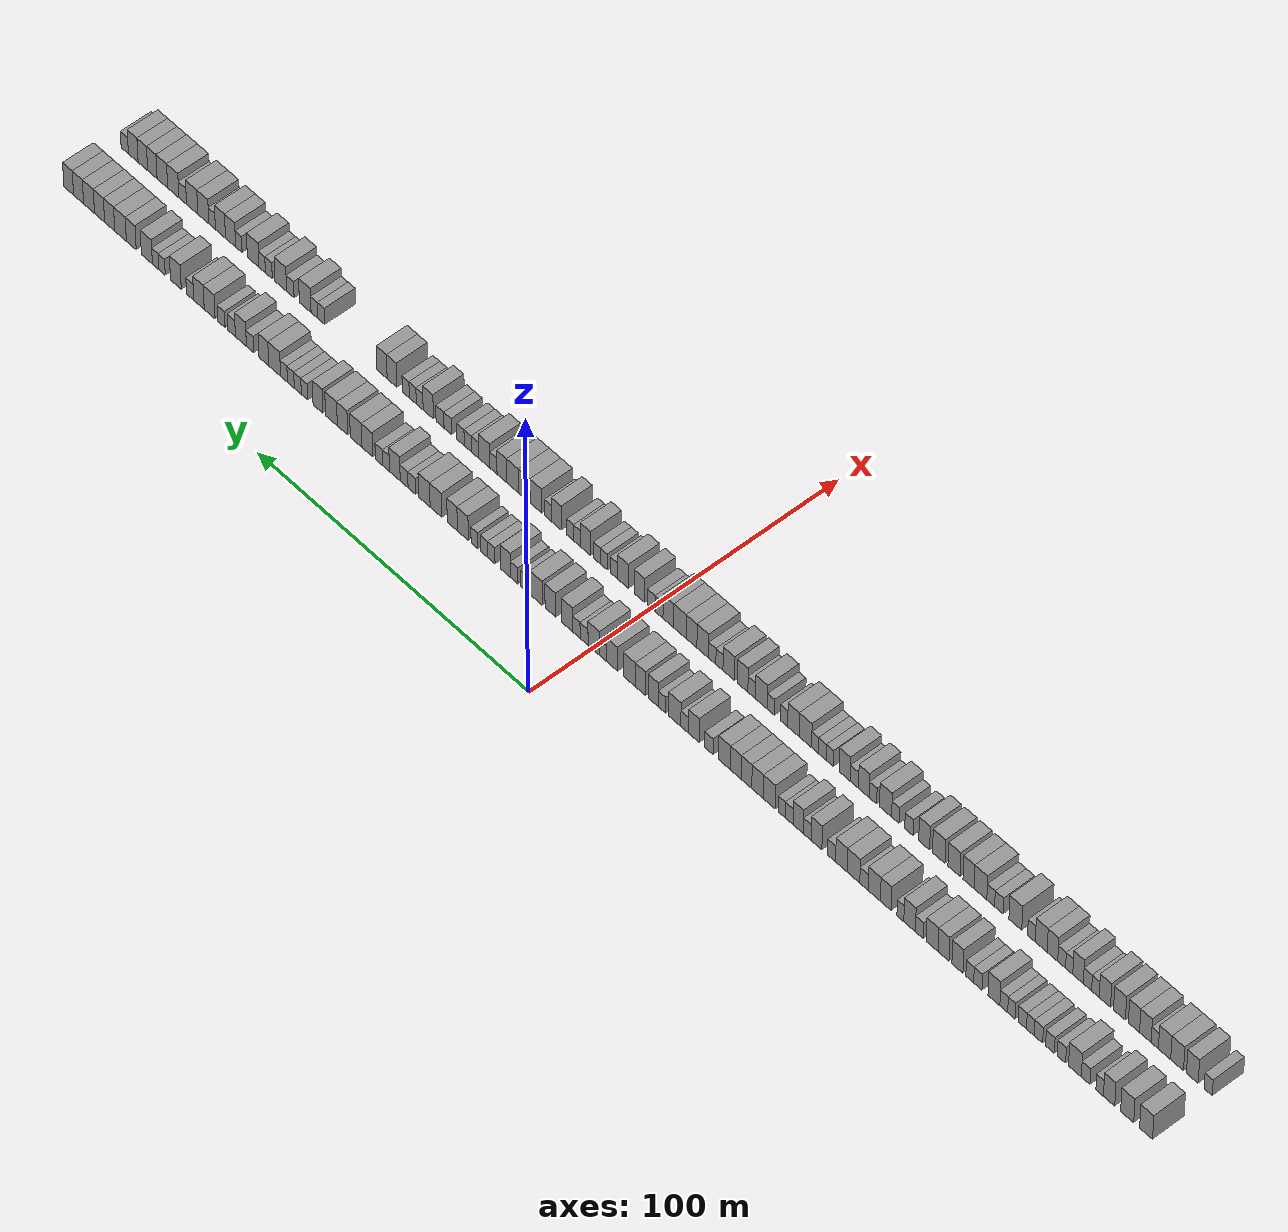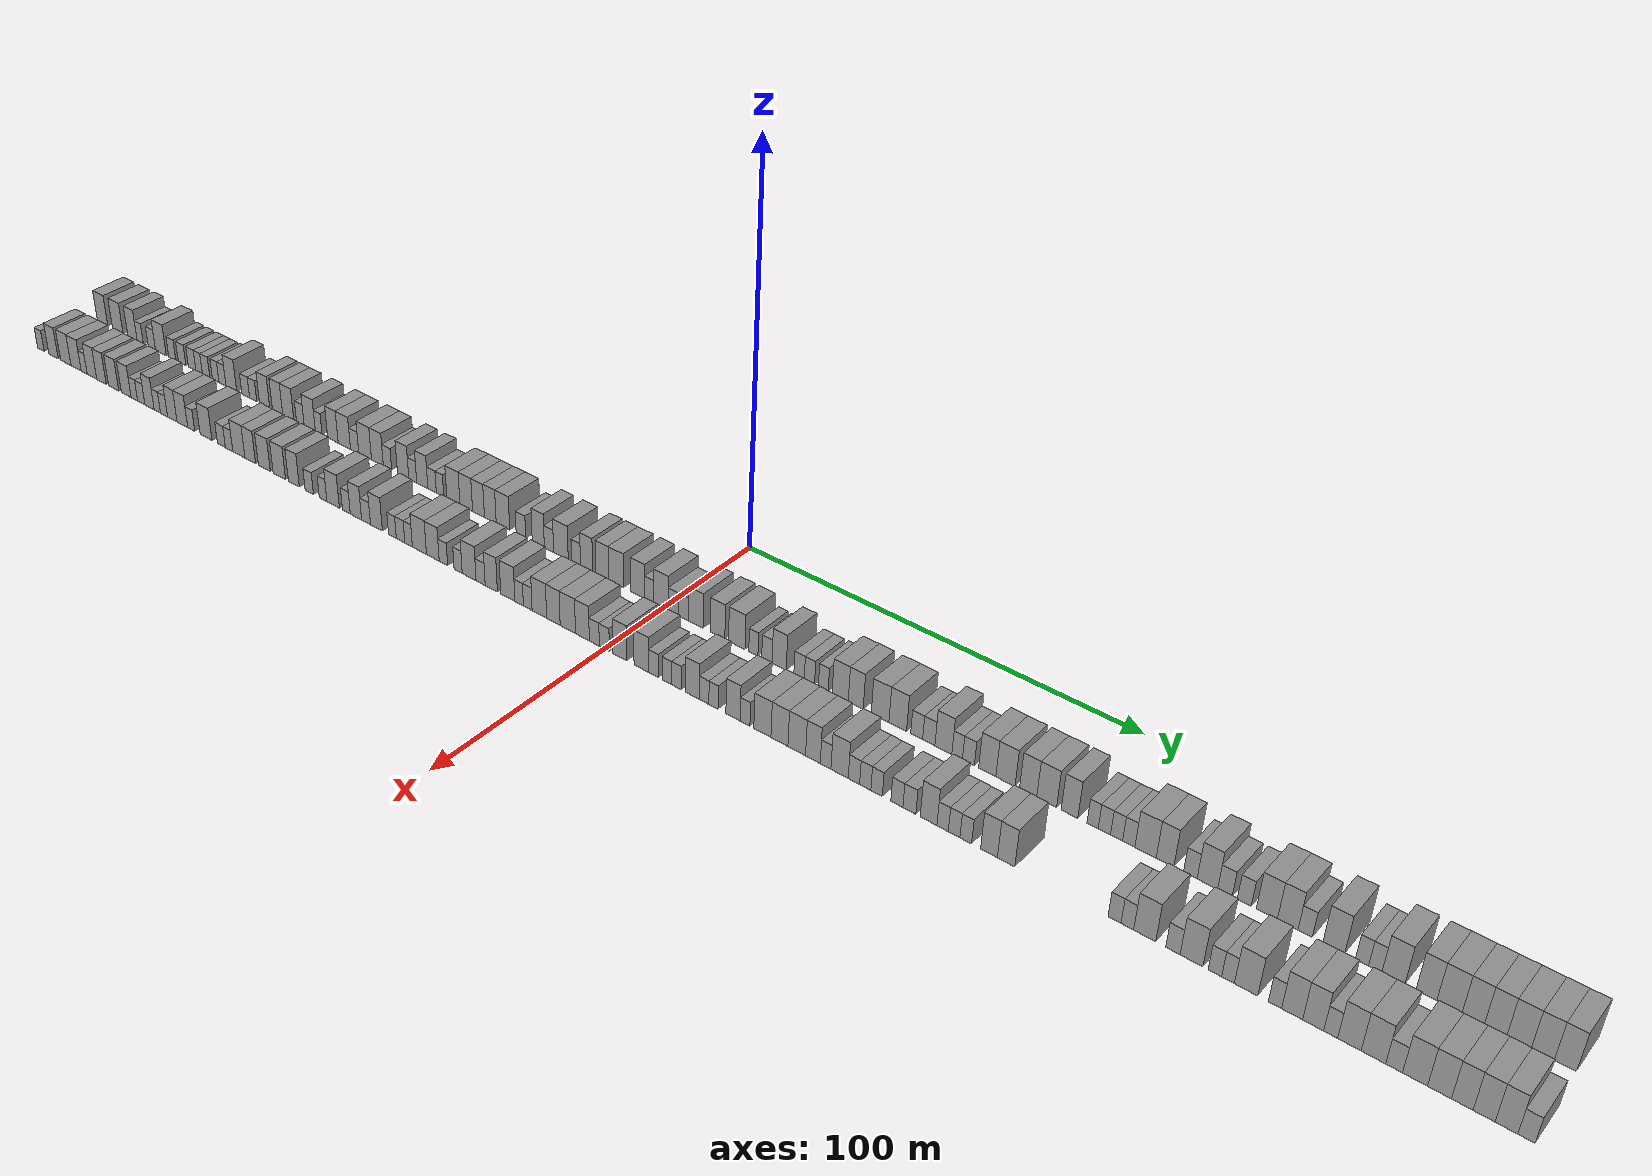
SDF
<sdf version="1.6">
 <world name="default">
  <scene>
   <sky><clouds><speed>12</speed></clouds></sky>
   <ambient>0.4 0.4 0.4 1</ambient>
   <background>0.7 0.7 0.7 1</background>
   <shadows>1</shadows>
  </scene>
  <gravity>0 0 -9.8066</gravity>
  <magnetic_field>6e-06 2.3e-05 -4.2e-05</magnetic_field>
  <physics default="0" name="default_physics" type="ode">
   <ode>
    <solver>
     <type>quick</type>
     <iters>10</iters>
     <sor>1.0</sor>
     <use_dynamic_moi_rescaling>0</use_dynamic_moi_rescaling>
    </solver>
    <constraints>
     <cfm>0</cfm>
     <erp>0.2</erp>
     <contact_max_correcting_vel>100</contact_max_correcting_vel>
     <contact_surface_layer>0.001</contact_surface_layer>
    </constraints>
   </ode>
   <max_step_size>0.004</max_step_size>
   <real_time_factor>1</real_time_factor>
   <real_time_update_rate>250</real_time_update_rate>
  </physics>
  <light name="sun" type="directional">
   <pose>0 0 10 0 0 0</pose>
   <diffuse>0.8 0.8 0.8 1</diffuse>
   <specular>0.2 0.2 0.2 1</specular>
   <attenuation>
    <range>1000</range>
    <constant>0.9</constant>
    <linear>0.01</linear>
    <quadratic>0.001</quadratic>
   </attenuation>
   <direction>-0.5 0.1 -0.9</direction>
  </light>
  <model name="building_1">
   <static>1</static>
   <pose>25.0000 -193.8158 0 0.000000 0.000000 0.000000</pose>
   <link name="link">
    <pose>0 0 4.50 0 0 0</pose>
    <collision name="collision"><geometry><box><size>10.0000 4.3684 9.0000</size></box></geometry></collision>
    <visual name="visual">
     <cast_shadows>0</cast_shadows>
     <geometry><box><size>10.0000 4.3684 9.0000</size></box></geometry>
     <material>
      <script>
       <uri>model://grey_wall/materials/scripts</uri>
       <uri>model://grey_wall/materials/textures</uri>
       <name>vrc/grey_wall</name>
      </script>
     </material>
    </visual>
   </link>
  </model>
  <model name="building_2">
   <static>1</static>
   <pose>25.0000 -187.4252 0 0.000000 0.000000 0.000000</pose>
   <link name="link">
    <pose>0 0 4.50 0 0 0</pose>
    <collision name="collision"><geometry><box><size>10.0000 4.4127 9.0000</size></box></geometry></collision>
    <visual name="visual">
     <cast_shadows>0</cast_shadows>
     <geometry><box><size>10.0000 4.4127 9.0000</size></box></geometry>
     <material>
      <script>
       <uri>model://grey_wall/materials/scripts</uri>
       <uri>model://grey_wall/materials/textures</uri>
       <name>vrc/grey_wall</name>
      </script>
     </material>
    </visual>
   </link>
  </model>
  <model name="building_3">
   <static>1</static>
   <pose>25.0000 -181.3065 0 0.000000 0.000000 0.000000</pose>
   <link name="link">
    <pose>0 0 4.50 0 0 0</pose>
    <collision name="collision"><geometry><box><size>10.0000 3.8246 9.0000</size></box></geometry></collision>
    <visual name="visual">
     <cast_shadows>0</cast_shadows>
     <geometry><box><size>10.0000 3.8246 9.0000</size></box></geometry>
     <material>
      <script>
       <uri>model://grey_wall/materials/scripts</uri>
       <uri>model://grey_wall/materials/textures</uri>
       <name>vrc/grey_wall</name>
      </script>
     </material>
    </visual>
   </link>
  </model>
  <model name="building_4">
   <static>1</static>
   <pose>25.0000 -178.1168 0 0.000000 0.000000 0.000000</pose>
   <link name="link">
    <pose>0 0 3.00 0 0 0</pose>
    <collision name="collision"><geometry><box><size>10.0000 2.5548 6.0000</size></box></geometry></collision>
    <visual name="visual">
     <cast_shadows>0</cast_shadows>
     <geometry><box><size>10.0000 2.5548 6.0000</size></box></geometry>
     <material>
      <script>
       <uri>model://grey_wall/materials/scripts</uri>
       <uri>model://grey_wall/materials/textures</uri>
       <name>vrc/grey_wall</name>
      </script>
     </material>
    </visual>
   </link>
  </model>
  <model name="building_5">
   <static>1</static>
   <pose>25.0000 -173.3668 0 0.000000 0.000000 0.000000</pose>
   <link name="link">
    <pose>0 0 3.00 0 0 0</pose>
    <collision name="collision"><geometry><box><size>10.0000 2.9451 6.0000</size></box></geometry></collision>
    <visual name="visual">
     <cast_shadows>0</cast_shadows>
     <geometry><box><size>10.0000 2.9451 6.0000</size></box></geometry>
     <material>
      <script>
       <uri>model://grey_wall/materials/scripts</uri>
       <uri>model://grey_wall/materials/textures</uri>
       <name>vrc/grey_wall</name>
      </script>
     </material>
    </visual>
   </link>
  </model>
  <model name="building_6">
   <static>1</static>
   <pose>25.0000 -169.7110 0 0.000000 0.000000 0.000000</pose>
   <link name="link">
    <pose>0 0 4.50 0 0 0</pose>
    <collision name="collision"><geometry><box><size>10.0000 4.3665 9.0000</size></box></geometry></collision>
    <visual name="visual">
     <cast_shadows>0</cast_shadows>
     <geometry><box><size>10.0000 4.3665 9.0000</size></box></geometry>
     <material>
      <script>
       <uri>model://grey_wall/materials/scripts</uri>
       <uri>model://grey_wall/materials/textures</uri>
       <name>vrc/grey_wall</name>
      </script>
     </material>
    </visual>
   </link>
  </model>
  <model name="building_7">
   <static>1</static>
   <pose>25.0000 -165.1141 0 0.000000 0.000000 0.000000</pose>
   <link name="link">
    <pose>0 0 3.00 0 0 0</pose>
    <collision name="collision"><geometry><box><size>10.0000 2.8274 6.0000</size></box></geometry></collision>
    <visual name="visual">
     <cast_shadows>0</cast_shadows>
     <geometry><box><size>10.0000 2.8274 6.0000</size></box></geometry>
     <material>
      <script>
       <uri>model://grey_wall/materials/scripts</uri>
       <uri>model://grey_wall/materials/textures</uri>
       <name>vrc/grey_wall</name>
      </script>
     </material>
    </visual>
   </link>
  </model>
  <model name="building_8">
   <static>1</static>
   <pose>25.0000 -161.2014 0 0.000000 0.000000 0.000000</pose>
   <link name="link">
    <pose>0 0 3.00 0 0 0</pose>
    <collision name="collision"><geometry><box><size>10.0000 2.9981 6.0000</size></box></geometry></collision>
    <visual name="visual">
     <cast_shadows>0</cast_shadows>
     <geometry><box><size>10.0000 2.9981 6.0000</size></box></geometry>
     <material>
      <script>
       <uri>model://grey_wall/materials/scripts</uri>
       <uri>model://grey_wall/materials/textures</uri>
       <name>vrc/grey_wall</name>
      </script>
     </material>
    </visual>
   </link>
  </model>
  <model name="building_9">
   <static>1</static>
   <pose>25.0000 -157.2229 0 0.000000 0.000000 0.000000</pose>
   <link name="link">
    <pose>0 0 3.00 0 0 0</pose>
    <collision name="collision"><geometry><box><size>10.0000 2.9589 6.0000</size></box></geometry></collision>
    <visual name="visual">
     <cast_shadows>0</cast_shadows>
     <geometry><box><size>10.0000 2.9589 6.0000</size></box></geometry>
     <material>
      <script>
       <uri>model://grey_wall/materials/scripts</uri>
       <uri>model://grey_wall/materials/textures</uri>
       <name>vrc/grey_wall</name>
      </script>
     </material>
    </visual>
   </link>
  </model>
  <model name="building_10">
   <static>1</static>
   <pose>25.0000 -154.4646 0 0.000000 0.000000 0.000000</pose>
   <link name="link">
    <pose>0 0 3.00 0 0 0</pose>
    <collision name="collision"><geometry><box><size>10.0000 2.5576 6.0000</size></box></geometry></collision>
    <visual name="visual">
     <cast_shadows>0</cast_shadows>
     <geometry><box><size>10.0000 2.5576 6.0000</size></box></geometry>
     <material>
      <script>
       <uri>model://grey_wall/materials/scripts</uri>
       <uri>model://grey_wall/materials/textures</uri>
       <name>vrc/grey_wall</name>
      </script>
     </material>
    </visual>
   </link>
  </model>
  <model name="building_11">
   <static>1</static>
   <pose>25.0000 -151.7313 0 0.000000 0.000000 0.000000</pose>
   <link name="link">
    <pose>0 0 3.00 0 0 0</pose>
    <collision name="collision"><geometry><box><size>10.0000 2.9090 6.0000</size></box></geometry></collision>
    <visual name="visual">
     <cast_shadows>0</cast_shadows>
     <geometry><box><size>10.0000 2.9090 6.0000</size></box></geometry>
     <material>
      <script>
       <uri>model://grey_wall/materials/scripts</uri>
       <uri>model://grey_wall/materials/textures</uri>
       <name>vrc/grey_wall</name>
      </script>
     </material>
    </visual>
   </link>
  </model>
  <model name="building_12">
   <static>1</static>
   <pose>25.0000 -148.0010 0 0.000000 0.000000 0.000000</pose>
   <link name="link">
    <pose>0 0 3.00 0 0 0</pose>
    <collision name="collision"><geometry><box><size>10.0000 2.5517 6.0000</size></box></geometry></collision>
    <visual name="visual">
     <cast_shadows>0</cast_shadows>
     <geometry><box><size>10.0000 2.5517 6.0000</size></box></geometry>
     <material>
      <script>
       <uri>model://grey_wall/materials/scripts</uri>
       <uri>model://grey_wall/materials/textures</uri>
       <name>vrc/grey_wall</name>
      </script>
     </material>
    </visual>
   </link>
  </model>
  <model name="building_13">
   <static>1</static>
   <pose>25.0000 -145.3806 0 0.000000 0.000000 0.000000</pose>
   <link name="link">
    <pose>0 0 3.00 0 0 0</pose>
    <collision name="collision"><geometry><box><size>10.0000 2.6890 6.0000</size></box></geometry></collision>
    <visual name="visual">
     <cast_shadows>0</cast_shadows>
     <geometry><box><size>10.0000 2.6890 6.0000</size></box></geometry>
     <material>
      <script>
       <uri>model://grey_wall/materials/scripts</uri>
       <uri>model://grey_wall/materials/textures</uri>
       <name>vrc/grey_wall</name>
      </script>
     </material>
    </visual>
   </link>
  </model>
  <model name="building_14">
   <static>1</static>
   <pose>25.0000 -141.9866 0 0.000000 0.000000 0.000000</pose>
   <link name="link">
    <pose>0 0 4.50 0 0 0</pose>
    <collision name="collision"><geometry><box><size>10.0000 4.0990 9.0000</size></box></geometry></collision>
    <visual name="visual">
     <cast_shadows>0</cast_shadows>
     <geometry><box><size>10.0000 4.0990 9.0000</size></box></geometry>
     <material>
      <script>
       <uri>model://grey_wall/materials/scripts</uri>
       <uri>model://grey_wall/materials/textures</uri>
       <name>vrc/grey_wall</name>
      </script>
     </material>
    </visual>
   </link>
  </model>
  <model name="building_15">
   <static>1</static>
   <pose>25.0000 -136.4802 0 0.000000 0.000000 0.000000</pose>
   <link name="link">
    <pose>0 0 3.00 0 0 0</pose>
    <collision name="collision"><geometry><box><size>10.0000 2.9137 6.0000</size></box></geometry></collision>
    <visual name="visual">
     <cast_shadows>0</cast_shadows>
     <geometry><box><size>10.0000 2.9137 6.0000</size></box></geometry>
     <material>
      <script>
       <uri>model://grey_wall/materials/scripts</uri>
       <uri>model://grey_wall/materials/textures</uri>
       <name>vrc/grey_wall</name>
      </script>
     </material>
    </visual>
   </link>
  </model>
  <model name="building_16">
   <static>1</static>
   <pose>25.0000 -133.6682 0 0.000000 0.000000 0.000000</pose>
   <link name="link">
    <pose>0 0 3.00 0 0 0</pose>
    <collision name="collision"><geometry><box><size>10.0000 2.7104 6.0000</size></box></geometry></collision>
    <visual name="visual">
     <cast_shadows>0</cast_shadows>
     <geometry><box><size>10.0000 2.7104 6.0000</size></box></geometry>
     <material>
      <script>
       <uri>model://grey_wall/materials/scripts</uri>
       <uri>model://grey_wall/materials/textures</uri>
       <name>vrc/grey_wall</name>
      </script>
     </material>
    </visual>
   </link>
  </model>
  <model name="building_17">
   <static>1</static>
   <pose>25.0000 -129.4004 0 0.000000 0.000000 0.000000</pose>
   <link name="link">
    <pose>0 0 4.50 0 0 0</pose>
    <collision name="collision"><geometry><box><size>10.0000 3.8253 9.0000</size></box></geometry></collision>
    <visual name="visual">
     <cast_shadows>0</cast_shadows>
     <geometry><box><size>10.0000 3.8253 9.0000</size></box></geometry>
     <material>
      <script>
       <uri>model://grey_wall/materials/scripts</uri>
       <uri>model://grey_wall/materials/textures</uri>
       <name>vrc/grey_wall</name>
      </script>
     </material>
    </visual>
   </link>
  </model>
  <model name="building_18">
   <static>1</static>
   <pose>25.0000 -124.5874 0 0.000000 0.000000 0.000000</pose>
   <link name="link">
    <pose>0 0 4.50 0 0 0</pose>
    <collision name="collision"><geometry><box><size>10.0000 3.8006 9.0000</size></box></geometry></collision>
    <visual name="visual">
     <cast_shadows>0</cast_shadows>
     <geometry><box><size>10.0000 3.8006 9.0000</size></box></geometry>
     <material>
      <script>
       <uri>model://grey_wall/materials/scripts</uri>
       <uri>model://grey_wall/materials/textures</uri>
       <name>vrc/grey_wall</name>
      </script>
     </material>
    </visual>
   </link>
  </model>
  <model name="building_19">
   <static>1</static>
   <pose>25.0000 -120.6496 0 0.000000 0.000000 0.000000</pose>
   <link name="link">
    <pose>0 0 4.50 0 0 0</pose>
    <collision name="collision"><geometry><box><size>10.0000 4.0750 9.0000</size></box></geometry></collision>
    <visual name="visual">
     <cast_shadows>0</cast_shadows>
     <geometry><box><size>10.0000 4.0750 9.0000</size></box></geometry>
     <material>
      <script>
       <uri>model://grey_wall/materials/scripts</uri>
       <uri>model://grey_wall/materials/textures</uri>
       <name>vrc/grey_wall</name>
      </script>
     </material>
    </visual>
   </link>
  </model>
  <model name="building_20">
   <static>1</static>
   <pose>25.0000 -116.2314 0 0.000000 0.000000 0.000000</pose>
   <link name="link">
    <pose>0 0 3.00 0 0 0</pose>
    <collision name="collision"><geometry><box><size>10.0000 2.7614 6.0000</size></box></geometry></collision>
    <visual name="visual">
     <cast_shadows>0</cast_shadows>
     <geometry><box><size>10.0000 2.7614 6.0000</size></box></geometry>
     <material>
      <script>
       <uri>model://grey_wall/materials/scripts</uri>
       <uri>model://grey_wall/materials/textures</uri>
       <name>vrc/grey_wall</name>
      </script>
     </material>
    </visual>
   </link>
  </model>
  <model name="building_21">
   <static>1</static>
   <pose>25.0000 -112.8315 0 0.000000 0.000000 0.000000</pose>
   <link name="link">
    <pose>0 0 4.50 0 0 0</pose>
    <collision name="collision"><geometry><box><size>10.0000 4.0385 9.0000</size></box></geometry></collision>
    <visual name="visual">
     <cast_shadows>0</cast_shadows>
     <geometry><box><size>10.0000 4.0385 9.0000</size></box></geometry>
     <material>
      <script>
       <uri>model://grey_wall/materials/scripts</uri>
       <uri>model://grey_wall/materials/textures</uri>
       <name>vrc/grey_wall</name>
      </script>
     </material>
    </visual>
   </link>
  </model>
  <model name="building_22">
   <static>1</static>
   <pose>25.0000 -109.6122 0 0.000000 0.000000 0.000000</pose>
   <link name="link">
    <pose>0 0 3.00 0 0 0</pose>
    <collision name="collision"><geometry><box><size>10.0000 2.4001 6.0000</size></box></geometry></collision>
    <visual name="visual">
     <cast_shadows>0</cast_shadows>
     <geometry><box><size>10.0000 2.4001 6.0000</size></box></geometry>
     <material>
      <script>
       <uri>model://grey_wall/materials/scripts</uri>
       <uri>model://grey_wall/materials/textures</uri>
       <name>vrc/grey_wall</name>
      </script>
     </material>
    </visual>
   </link>
  </model>
  <model name="building_23">
   <static>1</static>
   <pose>25.0000 -104.5498 0 0.000000 0.000000 0.000000</pose>
   <link name="link">
    <pose>0 0 4.50 0 0 0</pose>
    <collision name="collision"><geometry><box><size>10.0000 3.7247 9.0000</size></box></geometry></collision>
    <visual name="visual">
     <cast_shadows>0</cast_shadows>
     <geometry><box><size>10.0000 3.7247 9.0000</size></box></geometry>
     <material>
      <script>
       <uri>model://grey_wall/materials/scripts</uri>
       <uri>model://grey_wall/materials/textures</uri>
       <name>vrc/grey_wall</name>
      </script>
     </material>
    </visual>
   </link>
  </model>
  <model name="building_24">
   <static>1</static>
   <pose>25.0000 -100.5147 0 0.000000 0.000000 0.000000</pose>
   <link name="link">
    <pose>0 0 4.50 0 0 0</pose>
    <collision name="collision"><geometry><box><size>10.0000 4.3453 9.0000</size></box></geometry></collision>
    <visual name="visual">
     <cast_shadows>0</cast_shadows>
     <geometry><box><size>10.0000 4.3453 9.0000</size></box></geometry>
     <material>
      <script>
       <uri>model://grey_wall/materials/scripts</uri>
       <uri>model://grey_wall/materials/textures</uri>
       <name>vrc/grey_wall</name>
      </script>
     </material>
    </visual>
   </link>
  </model>
  <model name="building_25">
   <static>1</static>
   <pose>25.0000 -96.9032 0 0.000000 0.000000 0.000000</pose>
   <link name="link">
    <pose>0 0 3.00 0 0 0</pose>
    <collision name="collision"><geometry><box><size>10.0000 2.8777 6.0000</size></box></geometry></collision>
    <visual name="visual">
     <cast_shadows>0</cast_shadows>
     <geometry><box><size>10.0000 2.8777 6.0000</size></box></geometry>
     <material>
      <script>
       <uri>model://grey_wall/materials/scripts</uri>
       <uri>model://grey_wall/materials/textures</uri>
       <name>vrc/grey_wall</name>
      </script>
     </material>
    </visual>
   </link>
  </model>
  <model name="building_26">
   <static>1</static>
   <pose>25.0000 -93.2507 0 0.000000 0.000000 0.000000</pose>
   <link name="link">
    <pose>0 0 4.50 0 0 0</pose>
    <collision name="collision"><geometry><box><size>10.0000 4.4274 9.0000</size></box></geometry></collision>
    <visual name="visual">
     <cast_shadows>0</cast_shadows>
     <geometry><box><size>10.0000 4.4274 9.0000</size></box></geometry>
     <material>
      <script>
       <uri>model://grey_wall/materials/scripts</uri>
       <uri>model://grey_wall/materials/textures</uri>
       <name>vrc/grey_wall</name>
      </script>
     </material>
    </visual>
   </link>
  </model>
  <model name="building_27">
   <static>1</static>
   <pose>25.0000 -89.0107 0 0.000000 0.000000 0.000000</pose>
   <link name="link">
    <pose>0 0 4.50 0 0 0</pose>
    <collision name="collision"><geometry><box><size>10.0000 4.0526 9.0000</size></box></geometry></collision>
    <visual name="visual">
     <cast_shadows>0</cast_shadows>
     <geometry><box><size>10.0000 4.0526 9.0000</size></box></geometry>
     <material>
      <script>
       <uri>model://grey_wall/materials/scripts</uri>
       <uri>model://grey_wall/materials/textures</uri>
       <name>vrc/grey_wall</name>
      </script>
     </material>
    </visual>
   </link>
  </model>
  <model name="building_28">
   <static>1</static>
   <pose>25.0000 -85.5695 0 0.000000 0.000000 0.000000</pose>
   <link name="link">
    <pose>0 0 3.00 0 0 0</pose>
    <collision name="collision"><geometry><box><size>10.0000 2.8299 6.0000</size></box></geometry></collision>
    <visual name="visual">
     <cast_shadows>0</cast_shadows>
     <geometry><box><size>10.0000 2.8299 6.0000</size></box></geometry>
     <material>
      <script>
       <uri>model://grey_wall/materials/scripts</uri>
       <uri>model://grey_wall/materials/textures</uri>
       <name>vrc/grey_wall</name>
      </script>
     </material>
    </visual>
   </link>
  </model>
  <model name="building_29">
   <static>1</static>
   <pose>25.0000 -80.2502 0 0.000000 0.000000 0.000000</pose>
   <link name="link">
    <pose>0 0 4.50 0 0 0</pose>
    <collision name="collision"><geometry><box><size>10.0000 3.8086 9.0000</size></box></geometry></collision>
    <visual name="visual">
     <cast_shadows>0</cast_shadows>
     <geometry><box><size>10.0000 3.8086 9.0000</size></box></geometry>
     <material>
      <script>
       <uri>model://grey_wall/materials/scripts</uri>
       <uri>model://grey_wall/materials/textures</uri>
       <name>vrc/grey_wall</name>
      </script>
     </material>
    </visual>
   </link>
  </model>
  <model name="building_30">
   <static>1</static>
   <pose>25.0000 -77.0159 0 0.000000 0.000000 0.000000</pose>
   <link name="link">
    <pose>0 0 3.00 0 0 0</pose>
    <collision name="collision"><geometry><box><size>10.0000 2.6602 6.0000</size></box></geometry></collision>
    <visual name="visual">
     <cast_shadows>0</cast_shadows>
     <geometry><box><size>10.0000 2.6602 6.0000</size></box></geometry>
     <material>
      <script>
       <uri>model://grey_wall/materials/scripts</uri>
       <uri>model://grey_wall/materials/textures</uri>
       <name>vrc/grey_wall</name>
      </script>
     </material>
    </visual>
   </link>
  </model>
  <model name="building_31">
   <static>1</static>
   <pose>25.0000 -73.8317 0 0.000000 0.000000 0.000000</pose>
   <link name="link">
    <pose>0 0 4.50 0 0 0</pose>
    <collision name="collision"><geometry><box><size>10.0000 3.7082 9.0000</size></box></geometry></collision>
    <visual name="visual">
     <cast_shadows>0</cast_shadows>
     <geometry><box><size>10.0000 3.7082 9.0000</size></box></geometry>
     <material>
      <script>
       <uri>model://grey_wall/materials/scripts</uri>
       <uri>model://grey_wall/materials/textures</uri>
       <name>vrc/grey_wall</name>
      </script>
     </material>
    </visual>
   </link>
  </model>
  <model name="building_32">
   <static>1</static>
   <pose>25.0000 -70.5869 0 0.000000 0.000000 0.000000</pose>
   <link name="link">
    <pose>0 0 3.00 0 0 0</pose>
    <collision name="collision"><geometry><box><size>10.0000 2.7813 6.0000</size></box></geometry></collision>
    <visual name="visual">
     <cast_shadows>0</cast_shadows>
     <geometry><box><size>10.0000 2.7813 6.0000</size></box></geometry>
     <material>
      <script>
       <uri>model://grey_wall/materials/scripts</uri>
       <uri>model://grey_wall/materials/textures</uri>
       <name>vrc/grey_wall</name>
      </script>
     </material>
    </visual>
   </link>
  </model>
  <model name="building_33">
   <static>1</static>
   <pose>25.0000 -67.9731 0 0.000000 0.000000 0.000000</pose>
   <link name="link">
    <pose>0 0 3.00 0 0 0</pose>
    <collision name="collision"><geometry><box><size>10.0000 2.4463 6.0000</size></box></geometry></collision>
    <visual name="visual">
     <cast_shadows>0</cast_shadows>
     <geometry><box><size>10.0000 2.4463 6.0000</size></box></geometry>
     <material>
      <script>
       <uri>model://grey_wall/materials/scripts</uri>
       <uri>model://grey_wall/materials/textures</uri>
       <name>vrc/grey_wall</name>
      </script>
     </material>
    </visual>
   </link>
  </model>
  <model name="building_34">
   <static>1</static>
   <pose>25.0000 -63.6120 0 0.000000 0.000000 0.000000</pose>
   <link name="link">
    <pose>0 0 4.50 0 0 0</pose>
    <collision name="collision"><geometry><box><size>10.0000 4.2760 9.0000</size></box></geometry></collision>
    <visual name="visual">
     <cast_shadows>0</cast_shadows>
     <geometry><box><size>10.0000 4.2760 9.0000</size></box></geometry>
     <material>
      <script>
       <uri>model://grey_wall/materials/scripts</uri>
       <uri>model://grey_wall/materials/textures</uri>
       <name>vrc/grey_wall</name>
      </script>
     </material>
    </visual>
   </link>
  </model>
  <model name="building_35">
   <static>1</static>
   <pose>25.0000 -59.4427 0 0.000000 0.000000 0.000000</pose>
   <link name="link">
    <pose>0 0 4.50 0 0 0</pose>
    <collision name="collision"><geometry><box><size>10.0000 4.0625 9.0000</size></box></geometry></collision>
    <visual name="visual">
     <cast_shadows>0</cast_shadows>
     <geometry><box><size>10.0000 4.0625 9.0000</size></box></geometry>
     <material>
      <script>
       <uri>model://grey_wall/materials/scripts</uri>
       <uri>model://grey_wall/materials/textures</uri>
       <name>vrc/grey_wall</name>
      </script>
     </material>
    </visual>
   </link>
  </model>
  <model name="building_36">
   <static>1</static>
   <pose>25.0000 -55.5194 0 0.000000 0.000000 0.000000</pose>
   <link name="link">
    <pose>0 0 4.50 0 0 0</pose>
    <collision name="collision"><geometry><box><size>10.0000 3.7842 9.0000</size></box></geometry></collision>
    <visual name="visual">
     <cast_shadows>0</cast_shadows>
     <geometry><box><size>10.0000 3.7842 9.0000</size></box></geometry>
     <material>
      <script>
       <uri>model://grey_wall/materials/scripts</uri>
       <uri>model://grey_wall/materials/textures</uri>
       <name>vrc/grey_wall</name>
      </script>
     </material>
    </visual>
   </link>
  </model>
  <model name="building_37">
   <static>1</static>
   <pose>25.0000 -51.7592 0 0.000000 0.000000 0.000000</pose>
   <link name="link">
    <pose>0 0 4.50 0 0 0</pose>
    <collision name="collision"><geometry><box><size>10.0000 3.7362 9.0000</size></box></geometry></collision>
    <visual name="visual">
     <cast_shadows>0</cast_shadows>
     <geometry><box><size>10.0000 3.7362 9.0000</size></box></geometry>
     <material>
      <script>
       <uri>model://grey_wall/materials/scripts</uri>
       <uri>model://grey_wall/materials/textures</uri>
       <name>vrc/grey_wall</name>
      </script>
     </material>
    </visual>
   </link>
  </model>
  <model name="building_38">
   <static>1</static>
   <pose>25.0000 -47.7667 0 0.000000 0.000000 0.000000</pose>
   <link name="link">
    <pose>0 0 4.50 0 0 0</pose>
    <collision name="collision"><geometry><box><size>10.0000 4.2488 9.0000</size></box></geometry></collision>
    <visual name="visual">
     <cast_shadows>0</cast_shadows>
     <geometry><box><size>10.0000 4.2488 9.0000</size></box></geometry>
     <material>
      <script>
       <uri>model://grey_wall/materials/scripts</uri>
       <uri>model://grey_wall/materials/textures</uri>
       <name>vrc/grey_wall</name>
      </script>
     </material>
    </visual>
   </link>
  </model>
  <model name="building_39">
   <static>1</static>
   <pose>25.0000 -42.1554 0 0.000000 0.000000 0.000000</pose>
   <link name="link">
    <pose>0 0 3.00 0 0 0</pose>
    <collision name="collision"><geometry><box><size>10.0000 2.9738 6.0000</size></box></geometry></collision>
    <visual name="visual">
     <cast_shadows>0</cast_shadows>
     <geometry><box><size>10.0000 2.9738 6.0000</size></box></geometry>
     <material>
      <script>
       <uri>model://grey_wall/materials/scripts</uri>
       <uri>model://grey_wall/materials/textures</uri>
       <name>vrc/grey_wall</name>
      </script>
     </material>
    </visual>
   </link>
  </model>
  <model name="building_40">
   <static>1</static>
   <pose>25.0000 -36.8088 0 0.000000 0.000000 0.000000</pose>
   <link name="link">
    <pose>0 0 4.50 0 0 0</pose>
    <collision name="collision"><geometry><box><size>10.0000 3.7194 9.0000</size></box></geometry></collision>
    <visual name="visual">
     <cast_shadows>0</cast_shadows>
     <geometry><box><size>10.0000 3.7194 9.0000</size></box></geometry>
     <material>
      <script>
       <uri>model://grey_wall/materials/scripts</uri>
       <uri>model://grey_wall/materials/textures</uri>
       <name>vrc/grey_wall</name>
      </script>
     </material>
    </visual>
   </link>
  </model>
  <model name="building_41">
   <static>1</static>
   <pose>25.0000 -33.5397 0 0.000000 0.000000 0.000000</pose>
   <link name="link">
    <pose>0 0 3.00 0 0 0</pose>
    <collision name="collision"><geometry><box><size>10.0000 2.8187 6.0000</size></box></geometry></collision>
    <visual name="visual">
     <cast_shadows>0</cast_shadows>
     <geometry><box><size>10.0000 2.8187 6.0000</size></box></geometry>
     <material>
      <script>
       <uri>model://grey_wall/materials/scripts</uri>
       <uri>model://grey_wall/materials/textures</uri>
       <name>vrc/grey_wall</name>
      </script>
     </material>
    </visual>
   </link>
  </model>
  <model name="building_42">
   <static>1</static>
   <pose>25.0000 -29.9237 0 0.000000 0.000000 0.000000</pose>
   <link name="link">
    <pose>0 0 4.50 0 0 0</pose>
    <collision name="collision"><geometry><box><size>10.0000 4.4133 9.0000</size></box></geometry></collision>
    <visual name="visual">
     <cast_shadows>0</cast_shadows>
     <geometry><box><size>10.0000 4.4133 9.0000</size></box></geometry>
     <material>
      <script>
       <uri>model://grey_wall/materials/scripts</uri>
       <uri>model://grey_wall/materials/textures</uri>
       <name>vrc/grey_wall</name>
      </script>
     </material>
    </visual>
   </link>
  </model>
  <model name="building_43">
   <static>1</static>
   <pose>25.0000 -25.3851 0 0.000000 0.000000 0.000000</pose>
   <link name="link">
    <pose>0 0 3.00 0 0 0</pose>
    <collision name="collision"><geometry><box><size>10.0000 2.6640 6.0000</size></box></geometry></collision>
    <visual name="visual">
     <cast_shadows>0</cast_shadows>
     <geometry><box><size>10.0000 2.6640 6.0000</size></box></geometry>
     <material>
      <script>
       <uri>model://grey_wall/materials/scripts</uri>
       <uri>model://grey_wall/materials/textures</uri>
       <name>vrc/grey_wall</name>
      </script>
     </material>
    </visual>
   </link>
  </model>
  <model name="building_44">
   <static>1</static>
   <pose>25.0000 -22.2529 0 0.000000 0.000000 0.000000</pose>
   <link name="link">
    <pose>0 0 4.50 0 0 0</pose>
    <collision name="collision"><geometry><box><size>10.0000 3.6002 9.0000</size></box></geometry></collision>
    <visual name="visual">
     <cast_shadows>0</cast_shadows>
     <geometry><box><size>10.0000 3.6002 9.0000</size></box></geometry>
     <material>
      <script>
       <uri>model://grey_wall/materials/scripts</uri>
       <uri>model://grey_wall/materials/textures</uri>
       <name>vrc/grey_wall</name>
      </script>
     </material>
    </visual>
   </link>
  </model>
  <model name="building_45">
   <static>1</static>
   <pose>25.0000 -17.6138 0 0.000000 0.000000 0.000000</pose>
   <link name="link">
    <pose>0 0 4.50 0 0 0</pose>
    <collision name="collision"><geometry><box><size>10.0000 3.6782 9.0000</size></box></geometry></collision>
    <visual name="visual">
     <cast_shadows>0</cast_shadows>
     <geometry><box><size>10.0000 3.6782 9.0000</size></box></geometry>
     <material>
      <script>
       <uri>model://grey_wall/materials/scripts</uri>
       <uri>model://grey_wall/materials/textures</uri>
       <name>vrc/grey_wall</name>
      </script>
     </material>
    </visual>
   </link>
  </model>
  <model name="building_46">
   <static>1</static>
   <pose>25.0000 -13.5874 0 0.000000 0.000000 0.000000</pose>
   <link name="link">
    <pose>0 0 4.50 0 0 0</pose>
    <collision name="collision"><geometry><box><size>10.0000 4.3746 9.0000</size></box></geometry></collision>
    <visual name="visual">
     <cast_shadows>0</cast_shadows>
     <geometry><box><size>10.0000 4.3746 9.0000</size></box></geometry>
     <material>
      <script>
       <uri>model://grey_wall/materials/scripts</uri>
       <uri>model://grey_wall/materials/textures</uri>
       <name>vrc/grey_wall</name>
      </script>
     </material>
    </visual>
   </link>
  </model>
  <model name="building_47">
   <static>1</static>
   <pose>25.0000 -7.3509 0 0.000000 0.000000 0.000000</pose>
   <link name="link">
    <pose>0 0 4.50 0 0 0</pose>
    <collision name="collision"><geometry><box><size>10.0000 4.0982 9.0000</size></box></geometry></collision>
    <visual name="visual">
     <cast_shadows>0</cast_shadows>
     <geometry><box><size>10.0000 4.0982 9.0000</size></box></geometry>
     <material>
      <script>
       <uri>model://grey_wall/materials/scripts</uri>
       <uri>model://grey_wall/materials/textures</uri>
       <name>vrc/grey_wall</name>
      </script>
     </material>
    </visual>
   </link>
  </model>
  <model name="building_48">
   <static>1</static>
   <pose>25.0000 -4.0877 0 0.000000 0.000000 0.000000</pose>
   <link name="link">
    <pose>0 0 3.00 0 0 0</pose>
    <collision name="collision"><geometry><box><size>10.0000 2.4283 6.0000</size></box></geometry></collision>
    <visual name="visual">
     <cast_shadows>0</cast_shadows>
     <geometry><box><size>10.0000 2.4283 6.0000</size></box></geometry>
     <material>
      <script>
       <uri>model://grey_wall/materials/scripts</uri>
       <uri>model://grey_wall/materials/textures</uri>
       <name>vrc/grey_wall</name>
      </script>
     </material>
    </visual>
   </link>
  </model>
  <model name="building_49">
   <static>1</static>
   <pose>25.0000 -0.7692 0 0.000000 0.000000 0.000000</pose>
   <link name="link">
    <pose>0 0 4.50 0 0 0</pose>
    <collision name="collision"><geometry><box><size>10.0000 4.2088 9.0000</size></box></geometry></collision>
    <visual name="visual">
     <cast_shadows>0</cast_shadows>
     <geometry><box><size>10.0000 4.2088 9.0000</size></box></geometry>
     <material>
      <script>
       <uri>model://grey_wall/materials/scripts</uri>
       <uri>model://grey_wall/materials/textures</uri>
       <name>vrc/grey_wall</name>
      </script>
     </material>
    </visual>
   </link>
  </model>
  <model name="building_50">
   <static>1</static>
   <pose>25.0000 2.7833 0 0.000000 0.000000 0.000000</pose>
   <link name="link">
    <pose>0 0 3.00 0 0 0</pose>
    <collision name="collision"><geometry><box><size>10.0000 2.8960 6.0000</size></box></geometry></collision>
    <visual name="visual">
     <cast_shadows>0</cast_shadows>
     <geometry><box><size>10.0000 2.8960 6.0000</size></box></geometry>
     <material>
      <script>
       <uri>model://grey_wall/materials/scripts</uri>
       <uri>model://grey_wall/materials/textures</uri>
       <name>vrc/grey_wall</name>
      </script>
     </material>
    </visual>
   </link>
  </model>
  <model name="building_51">
   <static>1</static>
   <pose>25.0000 5.5601 0 0.000000 0.000000 0.000000</pose>
   <link name="link">
    <pose>0 0 3.00 0 0 0</pose>
    <collision name="collision"><geometry><box><size>10.0000 2.6575 6.0000</size></box></geometry></collision>
    <visual name="visual">
     <cast_shadows>0</cast_shadows>
     <geometry><box><size>10.0000 2.6575 6.0000</size></box></geometry>
     <material>
      <script>
       <uri>model://grey_wall/materials/scripts</uri>
       <uri>model://grey_wall/materials/textures</uri>
       <name>vrc/grey_wall</name>
      </script>
     </material>
    </visual>
   </link>
  </model>
  <model name="building_52">
   <static>1</static>
   <pose>25.0000 8.9630 0 0.000000 0.000000 0.000000</pose>
   <link name="link">
    <pose>0 0 4.50 0 0 0</pose>
    <collision name="collision"><geometry><box><size>10.0000 4.1483 9.0000</size></box></geometry></collision>
    <visual name="visual">
     <cast_shadows>0</cast_shadows>
     <geometry><box><size>10.0000 4.1483 9.0000</size></box></geometry>
     <material>
      <script>
       <uri>model://grey_wall/materials/scripts</uri>
       <uri>model://grey_wall/materials/textures</uri>
       <name>vrc/grey_wall</name>
      </script>
     </material>
    </visual>
   </link>
  </model>
  <model name="building_53">
   <static>1</static>
   <pose>25.0000 15.0030 0 0.000000 0.000000 0.000000</pose>
   <link name="link">
    <pose>0 0 4.50 0 0 0</pose>
    <collision name="collision"><geometry><box><size>10.0000 3.9316 9.0000</size></box></geometry></collision>
    <visual name="visual">
     <cast_shadows>0</cast_shadows>
     <geometry><box><size>10.0000 3.9316 9.0000</size></box></geometry>
     <material>
      <script>
       <uri>model://grey_wall/materials/scripts</uri>
       <uri>model://grey_wall/materials/textures</uri>
       <name>vrc/grey_wall</name>
      </script>
     </material>
    </visual>
   </link>
  </model>
  <model name="building_54">
   <static>1</static>
   <pose>25.0000 20.1888 0 0.000000 0.000000 0.000000</pose>
   <link name="link">
    <pose>0 0 4.50 0 0 0</pose>
    <collision name="collision"><geometry><box><size>10.0000 4.4401 9.0000</size></box></geometry></collision>
    <visual name="visual">
     <cast_shadows>0</cast_shadows>
     <geometry><box><size>10.0000 4.4401 9.0000</size></box></geometry>
     <material>
      <script>
       <uri>model://grey_wall/materials/scripts</uri>
       <uri>model://grey_wall/materials/textures</uri>
       <name>vrc/grey_wall</name>
      </script>
     </material>
    </visual>
   </link>
  </model>
  <model name="building_55">
   <static>1</static>
   <pose>25.0000 24.6258 0 0.000000 0.000000 0.000000</pose>
   <link name="link">
    <pose>0 0 3.00 0 0 0</pose>
    <collision name="collision"><geometry><box><size>10.0000 2.4338 6.0000</size></box></geometry></collision>
    <visual name="visual">
     <cast_shadows>0</cast_shadows>
     <geometry><box><size>10.0000 2.4338 6.0000</size></box></geometry>
     <material>
      <script>
       <uri>model://grey_wall/materials/scripts</uri>
       <uri>model://grey_wall/materials/textures</uri>
       <name>vrc/grey_wall</name>
      </script>
     </material>
    </visual>
   </link>
  </model>
  <model name="building_56">
   <static>1</static>
   <pose>25.0000 28.2052 0 0.000000 0.000000 0.000000</pose>
   <link name="link">
    <pose>0 0 3.00 0 0 0</pose>
    <collision name="collision"><geometry><box><size>10.0000 2.7251 6.0000</size></box></geometry></collision>
    <visual name="visual">
     <cast_shadows>0</cast_shadows>
     <geometry><box><size>10.0000 2.7251 6.0000</size></box></geometry>
     <material>
      <script>
       <uri>model://grey_wall/materials/scripts</uri>
       <uri>model://grey_wall/materials/textures</uri>
       <name>vrc/grey_wall</name>
      </script>
     </material>
    </visual>
   </link>
  </model>
  <model name="building_57">
   <static>1</static>
   <pose>25.0000 31.4204 0 0.000000 0.000000 0.000000</pose>
   <link name="link">
    <pose>0 0 4.50 0 0 0</pose>
    <collision name="collision"><geometry><box><size>10.0000 3.7054 9.0000</size></box></geometry></collision>
    <visual name="visual">
     <cast_shadows>0</cast_shadows>
     <geometry><box><size>10.0000 3.7054 9.0000</size></box></geometry>
     <material>
      <script>
       <uri>model://grey_wall/materials/scripts</uri>
       <uri>model://grey_wall/materials/textures</uri>
       <name>vrc/grey_wall</name>
      </script>
     </material>
    </visual>
   </link>
  </model>
  <model name="building_58">
   <static>1</static>
   <pose>25.0000 36.6185 0 0.000000 0.000000 0.000000</pose>
   <link name="link">
    <pose>0 0 3.00 0 0 0</pose>
    <collision name="collision"><geometry><box><size>10.0000 2.6908 6.0000</size></box></geometry></collision>
    <visual name="visual">
     <cast_shadows>0</cast_shadows>
     <geometry><box><size>10.0000 2.6908 6.0000</size></box></geometry>
     <material>
      <script>
       <uri>model://grey_wall/materials/scripts</uri>
       <uri>model://grey_wall/materials/textures</uri>
       <name>vrc/grey_wall</name>
      </script>
     </material>
    </visual>
   </link>
  </model>
  <model name="building_59">
   <static>1</static>
   <pose>25.0000 39.2777 0 0.000000 0.000000 0.000000</pose>
   <link name="link">
    <pose>0 0 3.00 0 0 0</pose>
    <collision name="collision"><geometry><box><size>10.0000 2.6276 6.0000</size></box></geometry></collision>
    <visual name="visual">
     <cast_shadows>0</cast_shadows>
     <geometry><box><size>10.0000 2.6276 6.0000</size></box></geometry>
     <material>
      <script>
       <uri>model://grey_wall/materials/scripts</uri>
       <uri>model://grey_wall/materials/textures</uri>
       <name>vrc/grey_wall</name>
      </script>
     </material>
    </visual>
   </link>
  </model>
  <model name="building_60">
   <static>1</static>
   <pose>25.0000 42.8340 0 0.000000 0.000000 0.000000</pose>
   <link name="link">
    <pose>0 0 3.00 0 0 0</pose>
    <collision name="collision"><geometry><box><size>10.0000 2.4851 6.0000</size></box></geometry></collision>
    <visual name="visual">
     <cast_shadows>0</cast_shadows>
     <geometry><box><size>10.0000 2.4851 6.0000</size></box></geometry>
     <material>
      <script>
       <uri>model://grey_wall/materials/scripts</uri>
       <uri>model://grey_wall/materials/textures</uri>
       <name>vrc/grey_wall</name>
      </script>
     </material>
    </visual>
   </link>
  </model>
  <model name="building_61">
   <static>1</static>
   <pose>25.0000 47.1062 0 0.000000 0.000000 0.000000</pose>
   <link name="link">
    <pose>0 0 4.50 0 0 0</pose>
    <collision name="collision"><geometry><box><size>10.0000 4.0592 9.0000</size></box></geometry></collision>
    <visual name="visual">
     <cast_shadows>0</cast_shadows>
     <geometry><box><size>10.0000 4.0592 9.0000</size></box></geometry>
     <material>
      <script>
       <uri>model://grey_wall/materials/scripts</uri>
       <uri>model://grey_wall/materials/textures</uri>
       <name>vrc/grey_wall</name>
      </script>
     </material>
    </visual>
   </link>
  </model>
  <model name="building_62">
   <static>1</static>
   <pose>25.0000 51.0010 0 0.000000 0.000000 0.000000</pose>
   <link name="link">
    <pose>0 0 4.50 0 0 0</pose>
    <collision name="collision"><geometry><box><size>10.0000 3.7304 9.0000</size></box></geometry></collision>
    <visual name="visual">
     <cast_shadows>0</cast_shadows>
     <geometry><box><size>10.0000 3.7304 9.0000</size></box></geometry>
     <material>
      <script>
       <uri>model://grey_wall/materials/scripts</uri>
       <uri>model://grey_wall/materials/textures</uri>
       <name>vrc/grey_wall</name>
      </script>
     </material>
    </visual>
   </link>
  </model>
  <model name="building_63">
   <static>1</static>
   <pose>25.0000 57.0351 0 0.000000 0.000000 0.000000</pose>
   <link name="link">
    <pose>0 0 4.50 0 0 0</pose>
    <collision name="collision"><geometry><box><size>10.0000 4.3378 9.0000</size></box></geometry></collision>
    <visual name="visual">
     <cast_shadows>0</cast_shadows>
     <geometry><box><size>10.0000 4.3378 9.0000</size></box></geometry>
     <material>
      <script>
       <uri>model://grey_wall/materials/scripts</uri>
       <uri>model://grey_wall/materials/textures</uri>
       <name>vrc/grey_wall</name>
      </script>
     </material>
    </visual>
   </link>
  </model>
  <model name="building_64">
   <static>1</static>
   <pose>25.0000 61.3493 0 0.000000 0.000000 0.000000</pose>
   <link name="link">
    <pose>0 0 4.50 0 0 0</pose>
    <collision name="collision"><geometry><box><size>10.0000 4.2907 9.0000</size></box></geometry></collision>
    <visual name="visual">
     <cast_shadows>0</cast_shadows>
     <geometry><box><size>10.0000 4.2907 9.0000</size></box></geometry>
     <material>
      <script>
       <uri>model://grey_wall/materials/scripts</uri>
       <uri>model://grey_wall/materials/textures</uri>
       <name>vrc/grey_wall</name>
      </script>
     </material>
    </visual>
   </link>
  </model>
  <model name="building_65">
   <static>1</static>
   <pose>25.0000 65.9351 0 0.000000 0.000000 0.000000</pose>
   <link name="link">
    <pose>0 0 3.00 0 0 0</pose>
    <collision name="collision"><geometry><box><size>10.0000 2.8809 6.0000</size></box></geometry></collision>
    <visual name="visual">
     <cast_shadows>0</cast_shadows>
     <geometry><box><size>10.0000 2.8809 6.0000</size></box></geometry>
     <material>
      <script>
       <uri>model://grey_wall/materials/scripts</uri>
       <uri>model://grey_wall/materials/textures</uri>
       <name>vrc/grey_wall</name>
      </script>
     </material>
    </visual>
   </link>
  </model>
  <model name="building_66">
   <static>1</static>
   <pose>25.0000 68.8346 0 0.000000 0.000000 0.000000</pose>
   <link name="link">
    <pose>0 0 3.00 0 0 0</pose>
    <collision name="collision"><geometry><box><size>10.0000 2.9181 6.0000</size></box></geometry></collision>
    <visual name="visual">
     <cast_shadows>0</cast_shadows>
     <geometry><box><size>10.0000 2.9181 6.0000</size></box></geometry>
     <material>
      <script>
       <uri>model://grey_wall/materials/scripts</uri>
       <uri>model://grey_wall/materials/textures</uri>
       <name>vrc/grey_wall</name>
      </script>
     </material>
    </visual>
   </link>
  </model>
  <model name="building_67">
   <static>1</static>
   <pose>25.0000 72.2965 0 0.000000 0.000000 0.000000</pose>
   <link name="link">
    <pose>0 0 4.50 0 0 0</pose>
    <collision name="collision"><geometry><box><size>10.0000 4.0057 9.0000</size></box></geometry></collision>
    <visual name="visual">
     <cast_shadows>0</cast_shadows>
     <geometry><box><size>10.0000 4.0057 9.0000</size></box></geometry>
     <material>
      <script>
       <uri>model://grey_wall/materials/scripts</uri>
       <uri>model://grey_wall/materials/textures</uri>
       <name>vrc/grey_wall</name>
      </script>
     </material>
    </visual>
   </link>
  </model>
  <model name="building_68">
   <static>1</static>
   <pose>25.0000 75.5396 0 0.000000 0.000000 0.000000</pose>
   <link name="link">
    <pose>0 0 3.00 0 0 0</pose>
    <collision name="collision"><geometry><box><size>10.0000 2.4805 6.0000</size></box></geometry></collision>
    <visual name="visual">
     <cast_shadows>0</cast_shadows>
     <geometry><box><size>10.0000 2.4805 6.0000</size></box></geometry>
     <material>
      <script>
       <uri>model://grey_wall/materials/scripts</uri>
       <uri>model://grey_wall/materials/textures</uri>
       <name>vrc/grey_wall</name>
      </script>
     </material>
    </visual>
   </link>
  </model>
  <model name="building_69">
   <static>1</static>
   <pose>25.0000 78.1669 0 0.000000 0.000000 0.000000</pose>
   <link name="link">
    <pose>0 0 3.00 0 0 0</pose>
    <collision name="collision"><geometry><box><size>10.0000 2.7742 6.0000</size></box></geometry></collision>
    <visual name="visual">
     <cast_shadows>0</cast_shadows>
     <geometry><box><size>10.0000 2.7742 6.0000</size></box></geometry>
     <material>
      <script>
       <uri>model://grey_wall/materials/scripts</uri>
       <uri>model://grey_wall/materials/textures</uri>
       <name>vrc/grey_wall</name>
      </script>
     </material>
    </visual>
   </link>
  </model>
  <model name="building_70">
   <static>1</static>
   <pose>25.0000 82.5401 0 0.000000 0.000000 0.000000</pose>
   <link name="link">
    <pose>0 0 4.50 0 0 0</pose>
    <collision name="collision"><geometry><box><size>10.0000 3.9721 9.0000</size></box></geometry></collision>
    <visual name="visual">
     <cast_shadows>0</cast_shadows>
     <geometry><box><size>10.0000 3.9721 9.0000</size></box></geometry>
     <material>
      <script>
       <uri>model://grey_wall/materials/scripts</uri>
       <uri>model://grey_wall/materials/textures</uri>
       <name>vrc/grey_wall</name>
      </script>
     </material>
    </visual>
   </link>
  </model>
  <model name="building_71">
   <static>1</static>
   <pose>25.0000 86.7129 0 0.000000 0.000000 0.000000</pose>
   <link name="link">
    <pose>0 0 4.50 0 0 0</pose>
    <collision name="collision"><geometry><box><size>10.0000 4.3736 9.0000</size></box></geometry></collision>
    <visual name="visual">
     <cast_shadows>0</cast_shadows>
     <geometry><box><size>10.0000 4.3736 9.0000</size></box></geometry>
     <material>
      <script>
       <uri>model://grey_wall/materials/scripts</uri>
       <uri>model://grey_wall/materials/textures</uri>
       <name>vrc/grey_wall</name>
      </script>
     </material>
    </visual>
   </link>
  </model>
  <model name="building_72">
   <static>1</static>
   <pose>25.0000 91.8360 0 0.000000 0.000000 0.000000</pose>
   <link name="link">
    <pose>0 0 4.50 0 0 0</pose>
    <collision name="collision"><geometry><box><size>10.0000 3.8725 9.0000</size></box></geometry></collision>
    <visual name="visual">
     <cast_shadows>0</cast_shadows>
     <geometry><box><size>10.0000 3.8725 9.0000</size></box></geometry>
     <material>
      <script>
       <uri>model://grey_wall/materials/scripts</uri>
       <uri>model://grey_wall/materials/textures</uri>
       <name>vrc/grey_wall</name>
      </script>
     </material>
    </visual>
   </link>
  </model>
  <model name="building_73">
   <static>1</static>
   <pose>25.0000 95.9816 0 0.000000 0.000000 0.000000</pose>
   <link name="link">
    <pose>0 0 4.50 0 0 0</pose>
    <collision name="collision"><geometry><box><size>10.0000 4.4187 9.0000</size></box></geometry></collision>
    <visual name="visual">
     <cast_shadows>0</cast_shadows>
     <geometry><box><size>10.0000 4.4187 9.0000</size></box></geometry>
     <material>
      <script>
       <uri>model://grey_wall/materials/scripts</uri>
       <uri>model://grey_wall/materials/textures</uri>
       <name>vrc/grey_wall</name>
      </script>
     </material>
    </visual>
   </link>
  </model>
  <model name="building_74">
   <static>1</static>
   <pose>25.0000 101.0312 0 0.000000 0.000000 0.000000</pose>
   <link name="link">
    <pose>0 0 4.50 0 0 0</pose>
    <collision name="collision"><geometry><box><size>10.0000 3.6806 9.0000</size></box></geometry></collision>
    <visual name="visual">
     <cast_shadows>0</cast_shadows>
     <geometry><box><size>10.0000 3.6806 9.0000</size></box></geometry>
     <material>
      <script>
       <uri>model://grey_wall/materials/scripts</uri>
       <uri>model://grey_wall/materials/textures</uri>
       <name>vrc/grey_wall</name>
      </script>
     </material>
    </visual>
   </link>
  </model>
  <model name="building_75">
   <static>1</static>
   <pose>25.0000 106.0870 0 0.000000 0.000000 0.000000</pose>
   <link name="link">
    <pose>0 0 3.00 0 0 0</pose>
    <collision name="collision"><geometry><box><size>10.0000 2.4309 6.0000</size></box></geometry></collision>
    <visual name="visual">
     <cast_shadows>0</cast_shadows>
     <geometry><box><size>10.0000 2.4309 6.0000</size></box></geometry>
     <material>
      <script>
       <uri>model://grey_wall/materials/scripts</uri>
       <uri>model://grey_wall/materials/textures</uri>
       <name>vrc/grey_wall</name>
      </script>
     </material>
    </visual>
   </link>
  </model>
  <model name="building_76">
   <static>1</static>
   <pose>25.0000 108.6257 0 0.000000 0.000000 0.000000</pose>
   <link name="link">
    <pose>0 0 3.00 0 0 0</pose>
    <collision name="collision"><geometry><box><size>10.0000 2.6464 6.0000</size></box></geometry></collision>
    <visual name="visual">
     <cast_shadows>0</cast_shadows>
     <geometry><box><size>10.0000 2.6464 6.0000</size></box></geometry>
     <material>
      <script>
       <uri>model://grey_wall/materials/scripts</uri>
       <uri>model://grey_wall/materials/textures</uri>
       <name>vrc/grey_wall</name>
      </script>
     </material>
    </visual>
   </link>
  </model>
  <model name="building_77">
   <static>1</static>
   <pose>25.0000 111.2392 0 0.000000 0.000000 0.000000</pose>
   <link name="link">
    <pose>0 0 3.00 0 0 0</pose>
    <collision name="collision"><geometry><box><size>10.0000 2.5808 6.0000</size></box></geometry></collision>
    <visual name="visual">
     <cast_shadows>0</cast_shadows>
     <geometry><box><size>10.0000 2.5808 6.0000</size></box></geometry>
     <material>
      <script>
       <uri>model://grey_wall/materials/scripts</uri>
       <uri>model://grey_wall/materials/textures</uri>
       <name>vrc/grey_wall</name>
      </script>
     </material>
    </visual>
   </link>
  </model>
  <model name="building_78">
   <static>1</static>
   <pose>25.0000 113.8284 0 0.000000 0.000000 0.000000</pose>
   <link name="link">
    <pose>0 0 3.00 0 0 0</pose>
    <collision name="collision"><geometry><box><size>10.0000 2.5975 6.0000</size></box></geometry></collision>
    <visual name="visual">
     <cast_shadows>0</cast_shadows>
     <geometry><box><size>10.0000 2.5975 6.0000</size></box></geometry>
     <material>
      <script>
       <uri>model://grey_wall/materials/scripts</uri>
       <uri>model://grey_wall/materials/textures</uri>
       <name>vrc/grey_wall</name>
      </script>
     </material>
    </visual>
   </link>
  </model>
  <model name="building_79">
   <static>1</static>
   <pose>25.0000 117.3661 0 0.000000 0.000000 0.000000</pose>
   <link name="link">
    <pose>0 0 4.50 0 0 0</pose>
    <collision name="collision"><geometry><box><size>10.0000 4.4780 9.0000</size></box></geometry></collision>
    <visual name="visual">
     <cast_shadows>0</cast_shadows>
     <geometry><box><size>10.0000 4.4780 9.0000</size></box></geometry>
     <material>
      <script>
       <uri>model://grey_wall/materials/scripts</uri>
       <uri>model://grey_wall/materials/textures</uri>
       <name>vrc/grey_wall</name>
      </script>
     </material>
    </visual>
   </link>
  </model>
  <model name="building_80">
   <static>1</static>
   <pose>25.0000 121.4425 0 0.000000 0.000000 0.000000</pose>
   <link name="link">
    <pose>0 0 4.50 0 0 0</pose>
    <collision name="collision"><geometry><box><size>10.0000 3.6749 9.0000</size></box></geometry></collision>
    <visual name="visual">
     <cast_shadows>0</cast_shadows>
     <geometry><box><size>10.0000 3.6749 9.0000</size></box></geometry>
     <material>
      <script>
       <uri>model://grey_wall/materials/scripts</uri>
       <uri>model://grey_wall/materials/textures</uri>
       <name>vrc/grey_wall</name>
      </script>
     </material>
    </visual>
   </link>
  </model>
  <model name="building_81">
   <static>1</static>
   <pose>25.0000 126.6723 0 0.000000 0.000000 0.000000</pose>
   <link name="link">
    <pose>0 0 3.00 0 0 0</pose>
    <collision name="collision"><geometry><box><size>10.0000 2.7845 6.0000</size></box></geometry></collision>
    <visual name="visual">
     <cast_shadows>0</cast_shadows>
     <geometry><box><size>10.0000 2.7845 6.0000</size></box></geometry>
     <material>
      <script>
       <uri>model://grey_wall/materials/scripts</uri>
       <uri>model://grey_wall/materials/textures</uri>
       <name>vrc/grey_wall</name>
      </script>
     </material>
    </visual>
   </link>
  </model>
  <model name="building_82">
   <static>1</static>
   <pose>25.0000 130.1458 0 0.000000 0.000000 0.000000</pose>
   <link name="link">
    <pose>0 0 4.50 0 0 0</pose>
    <collision name="collision"><geometry><box><size>10.0000 4.1626 9.0000</size></box></geometry></collision>
    <visual name="visual">
     <cast_shadows>0</cast_shadows>
     <geometry><box><size>10.0000 4.1626 9.0000</size></box></geometry>
     <material>
      <script>
       <uri>model://grey_wall/materials/scripts</uri>
       <uri>model://grey_wall/materials/textures</uri>
       <name>vrc/grey_wall</name>
      </script>
     </material>
    </visual>
   </link>
  </model>
  <model name="building_83">
   <static>1</static>
   <pose>25.0000 133.6976 0 0.000000 0.000000 0.000000</pose>
   <link name="link">
    <pose>0 0 3.00 0 0 0</pose>
    <collision name="collision"><geometry><box><size>10.0000 2.9409 6.0000</size></box></geometry></collision>
    <visual name="visual">
     <cast_shadows>0</cast_shadows>
     <geometry><box><size>10.0000 2.9409 6.0000</size></box></geometry>
     <material>
      <script>
       <uri>model://grey_wall/materials/scripts</uri>
       <uri>model://grey_wall/materials/textures</uri>
       <name>vrc/grey_wall</name>
      </script>
     </material>
    </visual>
   </link>
  </model>
  <model name="building_84">
   <static>1</static>
   <pose>25.0000 137.5640 0 0.000000 0.000000 0.000000</pose>
   <link name="link">
    <pose>0 0 3.00 0 0 0</pose>
    <collision name="collision"><geometry><box><size>10.0000 2.7920 6.0000</size></box></geometry></collision>
    <visual name="visual">
     <cast_shadows>0</cast_shadows>
     <geometry><box><size>10.0000 2.7920 6.0000</size></box></geometry>
     <material>
      <script>
       <uri>model://grey_wall/materials/scripts</uri>
       <uri>model://grey_wall/materials/textures</uri>
       <name>vrc/grey_wall</name>
      </script>
     </material>
    </visual>
   </link>
  </model>
  <model name="building_85">
   <static>1</static>
   <pose>25.0000 142.0333 0 0.000000 0.000000 0.000000</pose>
   <link name="link">
    <pose>0 0 4.50 0 0 0</pose>
    <collision name="collision"><geometry><box><size>10.0000 4.1465 9.0000</size></box></geometry></collision>
    <visual name="visual">
     <cast_shadows>0</cast_shadows>
     <geometry><box><size>10.0000 4.1465 9.0000</size></box></geometry>
     <material>
      <script>
       <uri>model://grey_wall/materials/scripts</uri>
       <uri>model://grey_wall/materials/textures</uri>
       <name>vrc/grey_wall</name>
      </script>
     </material>
    </visual>
   </link>
  </model>
  <model name="building_86">
   <static>1</static>
   <pose>25.0000 146.1061 0 0.000000 0.000000 0.000000</pose>
   <link name="link">
    <pose>0 0 4.50 0 0 0</pose>
    <collision name="collision"><geometry><box><size>10.0000 3.9990 9.0000</size></box></geometry></collision>
    <visual name="visual">
     <cast_shadows>0</cast_shadows>
     <geometry><box><size>10.0000 3.9990 9.0000</size></box></geometry>
     <material>
      <script>
       <uri>model://grey_wall/materials/scripts</uri>
       <uri>model://grey_wall/materials/textures</uri>
       <name>vrc/grey_wall</name>
      </script>
     </material>
    </visual>
   </link>
  </model>
  <model name="building_87">
   <static>1</static>
   <pose>25.0000 149.4916 0 0.000000 0.000000 0.000000</pose>
   <link name="link">
    <pose>0 0 3.00 0 0 0</pose>
    <collision name="collision"><geometry><box><size>10.0000 2.7720 6.0000</size></box></geometry></collision>
    <visual name="visual">
     <cast_shadows>0</cast_shadows>
     <geometry><box><size>10.0000 2.7720 6.0000</size></box></geometry>
     <material>
      <script>
       <uri>model://grey_wall/materials/scripts</uri>
       <uri>model://grey_wall/materials/textures</uri>
       <name>vrc/grey_wall</name>
      </script>
     </material>
    </visual>
   </link>
  </model>
  <model name="building_88">
   <static>1</static>
   <pose>25.0000 154.9476 0 0.000000 0.000000 0.000000</pose>
   <link name="link">
    <pose>0 0 4.50 0 0 0</pose>
    <collision name="collision"><geometry><box><size>10.0000 4.1400 9.0000</size></box></geometry></collision>
    <visual name="visual">
     <cast_shadows>0</cast_shadows>
     <geometry><box><size>10.0000 4.1400 9.0000</size></box></geometry>
     <material>
      <script>
       <uri>model://grey_wall/materials/scripts</uri>
       <uri>model://grey_wall/materials/textures</uri>
       <name>vrc/grey_wall</name>
      </script>
     </material>
    </visual>
   </link>
  </model>
  <model name="building_89">
   <static>1</static>
   <pose>25.0000 160.2522 0 0.000000 0.000000 0.000000</pose>
   <link name="link">
    <pose>0 0 3.00 0 0 0</pose>
    <collision name="collision"><geometry><box><size>10.0000 2.4693 6.0000</size></box></geometry></collision>
    <visual name="visual">
     <cast_shadows>0</cast_shadows>
     <geometry><box><size>10.0000 2.4693 6.0000</size></box></geometry>
     <material>
      <script>
       <uri>model://grey_wall/materials/scripts</uri>
       <uri>model://grey_wall/materials/textures</uri>
       <name>vrc/grey_wall</name>
      </script>
     </material>
    </visual>
   </link>
  </model>
  <model name="building_90">
   <static>1</static>
   <pose>25.0000 162.7166 0 0.000000 0.000000 0.000000</pose>
   <link name="link">
    <pose>0 0 3.00 0 0 0</pose>
    <collision name="collision"><geometry><box><size>10.0000 2.4597 6.0000</size></box></geometry></collision>
    <visual name="visual">
     <cast_shadows>0</cast_shadows>
     <geometry><box><size>10.0000 2.4597 6.0000</size></box></geometry>
     <material>
      <script>
       <uri>model://grey_wall/materials/scripts</uri>
       <uri>model://grey_wall/materials/textures</uri>
       <name>vrc/grey_wall</name>
      </script>
     </material>
    </visual>
   </link>
  </model>
  <model name="building_91">
   <static>1</static>
   <pose>25.0000 166.0668 0 0.000000 0.000000 0.000000</pose>
   <link name="link">
    <pose>0 0 4.50 0 0 0</pose>
    <collision name="collision"><geometry><box><size>10.0000 4.2406 9.0000</size></box></geometry></collision>
    <visual name="visual">
     <cast_shadows>0</cast_shadows>
     <geometry><box><size>10.0000 4.2406 9.0000</size></box></geometry>
     <material>
      <script>
       <uri>model://grey_wall/materials/scripts</uri>
       <uri>model://grey_wall/materials/textures</uri>
       <name>vrc/grey_wall</name>
      </script>
     </material>
    </visual>
   </link>
  </model>
  <model name="building_92">
   <static>1</static>
   <pose>25.0000 172.0715 0 0.000000 0.000000 0.000000</pose>
   <link name="link">
    <pose>0 0 4.50 0 0 0</pose>
    <collision name="collision"><geometry><box><size>10.0000 3.7690 9.0000</size></box></geometry></collision>
    <visual name="visual">
     <cast_shadows>0</cast_shadows>
     <geometry><box><size>10.0000 3.7690 9.0000</size></box></geometry>
     <material>
      <script>
       <uri>model://grey_wall/materials/scripts</uri>
       <uri>model://grey_wall/materials/textures</uri>
       <name>vrc/grey_wall</name>
      </script>
     </material>
    </visual>
   </link>
  </model>
  <model name="building_93">
   <static>1</static>
   <pose>25.0000 176.1982 0 0.000000 0.000000 0.000000</pose>
   <link name="link">
    <pose>0 0 4.50 0 0 0</pose>
    <collision name="collision"><geometry><box><size>10.0000 4.4844 9.0000</size></box></geometry></collision>
    <visual name="visual">
     <cast_shadows>0</cast_shadows>
     <geometry><box><size>10.0000 4.4844 9.0000</size></box></geometry>
     <material>
      <script>
       <uri>model://grey_wall/materials/scripts</uri>
       <uri>model://grey_wall/materials/textures</uri>
       <name>vrc/grey_wall</name>
      </script>
     </material>
    </visual>
   </link>
  </model>
  <model name="building_94">
   <static>1</static>
   <pose>25.0000 180.4055 0 0.000000 0.000000 0.000000</pose>
   <link name="link">
    <pose>0 0 4.50 0 0 0</pose>
    <collision name="collision"><geometry><box><size>10.0000 3.9302 9.0000</size></box></geometry></collision>
    <visual name="visual">
     <cast_shadows>0</cast_shadows>
     <geometry><box><size>10.0000 3.9302 9.0000</size></box></geometry>
     <material>
      <script>
       <uri>model://grey_wall/materials/scripts</uri>
       <uri>model://grey_wall/materials/textures</uri>
       <name>vrc/grey_wall</name>
      </script>
     </material>
    </visual>
   </link>
  </model>
  <model name="building_95">
   <static>1</static>
   <pose>25.0000 184.3220 0 0.000000 0.000000 0.000000</pose>
   <link name="link">
    <pose>0 0 4.50 0 0 0</pose>
    <collision name="collision"><geometry><box><size>10.0000 3.9027 9.0000</size></box></geometry></collision>
    <visual name="visual">
     <cast_shadows>0</cast_shadows>
     <geometry><box><size>10.0000 3.9027 9.0000</size></box></geometry>
     <material>
      <script>
       <uri>model://grey_wall/materials/scripts</uri>
       <uri>model://grey_wall/materials/textures</uri>
       <name>vrc/grey_wall</name>
      </script>
     </material>
    </visual>
   </link>
  </model>
  <model name="building_96">
   <static>1</static>
   <pose>25.0000 188.3840 0 0.000000 0.000000 0.000000</pose>
   <link name="link">
    <pose>0 0 4.50 0 0 0</pose>
    <collision name="collision"><geometry><box><size>10.0000 4.2213 9.0000</size></box></geometry></collision>
    <visual name="visual">
     <cast_shadows>0</cast_shadows>
     <geometry><box><size>10.0000 4.2213 9.0000</size></box></geometry>
     <material>
      <script>
       <uri>model://grey_wall/materials/scripts</uri>
       <uri>model://grey_wall/materials/textures</uri>
       <name>vrc/grey_wall</name>
      </script>
     </material>
    </visual>
   </link>
  </model>
  <model name="building_97">
   <static>1</static>
   <pose>25.0000 192.4436 0 0.000000 0.000000 0.000000</pose>
   <link name="link">
    <pose>0 0 4.50 0 0 0</pose>
    <collision name="collision"><geometry><box><size>10.0000 3.8978 9.0000</size></box></geometry></collision>
    <visual name="visual">
     <cast_shadows>0</cast_shadows>
     <geometry><box><size>10.0000 3.8978 9.0000</size></box></geometry>
     <material>
      <script>
       <uri>model://grey_wall/materials/scripts</uri>
       <uri>model://grey_wall/materials/textures</uri>
       <name>vrc/grey_wall</name>
      </script>
     </material>
    </visual>
   </link>
  </model>
  <model name="building_98">
   <static>1</static>
   <pose>25.0000 196.2651 0 0.000000 0.000000 0.000000</pose>
   <link name="link">
    <pose>0 0 4.50 0 0 0</pose>
    <collision name="collision"><geometry><box><size>10.0000 3.7453 9.0000</size></box></geometry></collision>
    <visual name="visual">
     <cast_shadows>0</cast_shadows>
     <geometry><box><size>10.0000 3.7453 9.0000</size></box></geometry>
     <material>
      <script>
       <uri>model://grey_wall/materials/scripts</uri>
       <uri>model://grey_wall/materials/textures</uri>
       <name>vrc/grey_wall</name>
      </script>
     </material>
    </visual>
   </link>
  </model>
  <model name="building_99">
   <static>1</static>
   <pose>44.0000 -194.6192 0 0.000000 0.000000 0.000000</pose>
   <link name="link">
    <pose>0 0 3.00 0 0 0</pose>
    <collision name="collision"><geometry><box><size>10.0000 2.7616 6.0000</size></box></geometry></collision>
    <visual name="visual">
     <cast_shadows>0</cast_shadows>
     <geometry><box><size>10.0000 2.7616 6.0000</size></box></geometry>
     <material>
      <script>
       <uri>model://grey_wall/materials/scripts</uri>
       <uri>model://grey_wall/materials/textures</uri>
       <name>vrc/grey_wall</name>
      </script>
     </material>
    </visual>
   </link>
  </model>
  <model name="building_100">
   <static>1</static>
   <pose>44.0000 -189.2688 0 0.000000 0.000000 0.000000</pose>
   <link name="link">
    <pose>0 0 4.50 0 0 0</pose>
    <collision name="collision"><geometry><box><size>10.0000 3.9391 9.0000</size></box></geometry></collision>
    <visual name="visual">
     <cast_shadows>0</cast_shadows>
     <geometry><box><size>10.0000 3.9391 9.0000</size></box></geometry>
     <material>
      <script>
       <uri>model://grey_wall/materials/scripts</uri>
       <uri>model://grey_wall/materials/textures</uri>
       <name>vrc/grey_wall</name>
      </script>
     </material>
    </visual>
   </link>
  </model>
  <model name="building_101">
   <static>1</static>
   <pose>44.0000 -184.1315 0 0.000000 0.000000 0.000000</pose>
   <link name="link">
    <pose>0 0 4.50 0 0 0</pose>
    <collision name="collision"><geometry><box><size>10.0000 4.3356 9.0000</size></box></geometry></collision>
    <visual name="visual">
     <cast_shadows>0</cast_shadows>
     <geometry><box><size>10.0000 4.3356 9.0000</size></box></geometry>
     <material>
      <script>
       <uri>model://grey_wall/materials/scripts</uri>
       <uri>model://grey_wall/materials/textures</uri>
       <name>vrc/grey_wall</name>
      </script>
     </material>
    </visual>
   </link>
  </model>
  <model name="building_102">
   <static>1</static>
   <pose>44.0000 -179.8727 0 0.000000 0.000000 0.000000</pose>
   <link name="link">
    <pose>0 0 4.50 0 0 0</pose>
    <collision name="collision"><geometry><box><size>10.0000 4.1820 9.0000</size></box></geometry></collision>
    <visual name="visual">
     <cast_shadows>0</cast_shadows>
     <geometry><box><size>10.0000 4.1820 9.0000</size></box></geometry>
     <material>
      <script>
       <uri>model://grey_wall/materials/scripts</uri>
       <uri>model://grey_wall/materials/textures</uri>
       <name>vrc/grey_wall</name>
      </script>
     </material>
    </visual>
   </link>
  </model>
  <model name="building_103">
   <static>1</static>
   <pose>44.0000 -176.5561 0 0.000000 0.000000 0.000000</pose>
   <link name="link">
    <pose>0 0 3.00 0 0 0</pose>
    <collision name="collision"><geometry><box><size>10.0000 2.4511 6.0000</size></box></geometry></collision>
    <visual name="visual">
     <cast_shadows>0</cast_shadows>
     <geometry><box><size>10.0000 2.4511 6.0000</size></box></geometry>
     <material>
      <script>
       <uri>model://grey_wall/materials/scripts</uri>
       <uri>model://grey_wall/materials/textures</uri>
       <name>vrc/grey_wall</name>
      </script>
     </material>
    </visual>
   </link>
  </model>
  <model name="building_104">
   <static>1</static>
   <pose>44.0000 -173.3631 0 0.000000 0.000000 0.000000</pose>
   <link name="link">
    <pose>0 0 4.50 0 0 0</pose>
    <collision name="collision"><geometry><box><size>10.0000 3.9349 9.0000</size></box></geometry></collision>
    <visual name="visual">
     <cast_shadows>0</cast_shadows>
     <geometry><box><size>10.0000 3.9349 9.0000</size></box></geometry>
     <material>
      <script>
       <uri>model://grey_wall/materials/scripts</uri>
       <uri>model://grey_wall/materials/textures</uri>
       <name>vrc/grey_wall</name>
      </script>
     </material>
    </visual>
   </link>
  </model>
  <model name="building_105">
   <static>1</static>
   <pose>44.0000 -169.4930 0 0.000000 0.000000 0.000000</pose>
   <link name="link">
    <pose>0 0 4.50 0 0 0</pose>
    <collision name="collision"><geometry><box><size>10.0000 3.8055 9.0000</size></box></geometry></collision>
    <visual name="visual">
     <cast_shadows>0</cast_shadows>
     <geometry><box><size>10.0000 3.8055 9.0000</size></box></geometry>
     <material>
      <script>
       <uri>model://grey_wall/materials/scripts</uri>
       <uri>model://grey_wall/materials/textures</uri>
       <name>vrc/grey_wall</name>
      </script>
     </material>
    </visual>
   </link>
  </model>
  <model name="building_106">
   <static>1</static>
   <pose>44.0000 -164.5534 0 0.000000 0.000000 0.000000</pose>
   <link name="link">
    <pose>0 0 4.50 0 0 0</pose>
    <collision name="collision"><geometry><box><size>10.0000 4.0736 9.0000</size></box></geometry></collision>
    <visual name="visual">
     <cast_shadows>0</cast_shadows>
     <geometry><box><size>10.0000 4.0736 9.0000</size></box></geometry>
     <material>
      <script>
       <uri>model://grey_wall/materials/scripts</uri>
       <uri>model://grey_wall/materials/textures</uri>
       <name>vrc/grey_wall</name>
      </script>
     </material>
    </visual>
   </link>
  </model>
  <model name="building_107">
   <static>1</static>
   <pose>44.0000 -159.5741 0 0.000000 0.000000 0.000000</pose>
   <link name="link">
    <pose>0 0 4.50 0 0 0</pose>
    <collision name="collision"><geometry><box><size>10.0000 3.8849 9.0000</size></box></geometry></collision>
    <visual name="visual">
     <cast_shadows>0</cast_shadows>
     <geometry><box><size>10.0000 3.8849 9.0000</size></box></geometry>
     <material>
      <script>
       <uri>model://grey_wall/materials/scripts</uri>
       <uri>model://grey_wall/materials/textures</uri>
       <name>vrc/grey_wall</name>
      </script>
     </material>
    </visual>
   </link>
  </model>
  <model name="building_108">
   <static>1</static>
   <pose>44.0000 -156.3396 0 0.000000 0.000000 0.000000</pose>
   <link name="link">
    <pose>0 0 3.00 0 0 0</pose>
    <collision name="collision"><geometry><box><size>10.0000 2.5842 6.0000</size></box></geometry></collision>
    <visual name="visual">
     <cast_shadows>0</cast_shadows>
     <geometry><box><size>10.0000 2.5842 6.0000</size></box></geometry>
     <material>
      <script>
       <uri>model://grey_wall/materials/scripts</uri>
       <uri>model://grey_wall/materials/textures</uri>
       <name>vrc/grey_wall</name>
      </script>
     </material>
    </visual>
   </link>
  </model>
  <model name="building_109">
   <static>1</static>
   <pose>44.0000 -153.6319 0 0.000000 0.000000 0.000000</pose>
   <link name="link">
    <pose>0 0 3.00 0 0 0</pose>
    <collision name="collision"><geometry><box><size>10.0000 2.8313 6.0000</size></box></geometry></collision>
    <visual name="visual">
     <cast_shadows>0</cast_shadows>
     <geometry><box><size>10.0000 2.8313 6.0000</size></box></geometry>
     <material>
      <script>
       <uri>model://grey_wall/materials/scripts</uri>
       <uri>model://grey_wall/materials/textures</uri>
       <name>vrc/grey_wall</name>
      </script>
     </material>
    </visual>
   </link>
  </model>
  <model name="building_110">
   <static>1</static>
   <pose>44.0000 -150.4083 0 0.000000 0.000000 0.000000</pose>
   <link name="link">
    <pose>0 0 4.50 0 0 0</pose>
    <collision name="collision"><geometry><box><size>10.0000 3.6159 9.0000</size></box></geometry></collision>
    <visual name="visual">
     <cast_shadows>0</cast_shadows>
     <geometry><box><size>10.0000 3.6159 9.0000</size></box></geometry>
     <material>
      <script>
       <uri>model://grey_wall/materials/scripts</uri>
       <uri>model://grey_wall/materials/textures</uri>
       <name>vrc/grey_wall</name>
      </script>
     </material>
    </visual>
   </link>
  </model>
  <model name="building_111">
   <static>1</static>
   <pose>44.0000 -147.3682 0 0.000000 0.000000 0.000000</pose>
   <link name="link">
    <pose>0 0 3.00 0 0 0</pose>
    <collision name="collision"><geometry><box><size>10.0000 2.4643 6.0000</size></box></geometry></collision>
    <visual name="visual">
     <cast_shadows>0</cast_shadows>
     <geometry><box><size>10.0000 2.4643 6.0000</size></box></geometry>
     <material>
      <script>
       <uri>model://grey_wall/materials/scripts</uri>
       <uri>model://grey_wall/materials/textures</uri>
       <name>vrc/grey_wall</name>
      </script>
     </material>
    </visual>
   </link>
  </model>
  <model name="building_112">
   <static>1</static>
   <pose>44.0000 -144.7877 0 0.000000 0.000000 0.000000</pose>
   <link name="link">
    <pose>0 0 3.00 0 0 0</pose>
    <collision name="collision"><geometry><box><size>10.0000 2.6968 6.0000</size></box></geometry></collision>
    <visual name="visual">
     <cast_shadows>0</cast_shadows>
     <geometry><box><size>10.0000 2.6968 6.0000</size></box></geometry>
     <material>
      <script>
       <uri>model://grey_wall/materials/scripts</uri>
       <uri>model://grey_wall/materials/textures</uri>
       <name>vrc/grey_wall</name>
      </script>
     </material>
    </visual>
   </link>
  </model>
  <model name="building_113">
   <static>1</static>
   <pose>44.0000 -141.6144 0 0.000000 0.000000 0.000000</pose>
   <link name="link">
    <pose>0 0 4.50 0 0 0</pose>
    <collision name="collision"><geometry><box><size>10.0000 3.6499 9.0000</size></box></geometry></collision>
    <visual name="visual">
     <cast_shadows>0</cast_shadows>
     <geometry><box><size>10.0000 3.6499 9.0000</size></box></geometry>
     <material>
      <script>
       <uri>model://grey_wall/materials/scripts</uri>
       <uri>model://grey_wall/materials/textures</uri>
       <name>vrc/grey_wall</name>
      </script>
     </material>
    </visual>
   </link>
  </model>
  <model name="building_114">
   <static>1</static>
   <pose>44.0000 -137.7563 0 0.000000 0.000000 0.000000</pose>
   <link name="link">
    <pose>0 0 4.50 0 0 0</pose>
    <collision name="collision"><geometry><box><size>10.0000 4.0663 9.0000</size></box></geometry></collision>
    <visual name="visual">
     <cast_shadows>0</cast_shadows>
     <geometry><box><size>10.0000 4.0663 9.0000</size></box></geometry>
     <material>
      <script>
       <uri>model://grey_wall/materials/scripts</uri>
       <uri>model://grey_wall/materials/textures</uri>
       <name>vrc/grey_wall</name>
      </script>
     </material>
    </visual>
   </link>
  </model>
  <model name="building_115">
   <static>1</static>
   <pose>44.0000 -134.3858 0 0.000000 0.000000 0.000000</pose>
   <link name="link">
    <pose>0 0 3.00 0 0 0</pose>
    <collision name="collision"><geometry><box><size>10.0000 2.6746 6.0000</size></box></geometry></collision>
    <visual name="visual">
     <cast_shadows>0</cast_shadows>
     <geometry><box><size>10.0000 2.6746 6.0000</size></box></geometry>
     <material>
      <script>
       <uri>model://grey_wall/materials/scripts</uri>
       <uri>model://grey_wall/materials/textures</uri>
       <name>vrc/grey_wall</name>
      </script>
     </material>
    </visual>
   </link>
  </model>
  <model name="building_116">
   <static>1</static>
   <pose>44.0000 -128.8311 0 0.000000 0.000000 0.000000</pose>
   <link name="link">
    <pose>0 0 4.50 0 0 0</pose>
    <collision name="collision"><geometry><box><size>10.0000 4.4349 9.0000</size></box></geometry></collision>
    <visual name="visual">
     <cast_shadows>0</cast_shadows>
     <geometry><box><size>10.0000 4.4349 9.0000</size></box></geometry>
     <material>
      <script>
       <uri>model://grey_wall/materials/scripts</uri>
       <uri>model://grey_wall/materials/textures</uri>
       <name>vrc/grey_wall</name>
      </script>
     </material>
    </visual>
   </link>
  </model>
  <model name="building_117">
   <static>1</static>
   <pose>44.0000 -123.1454 0 0.000000 0.000000 0.000000</pose>
   <link name="link">
    <pose>0 0 3.00 0 0 0</pose>
    <collision name="collision"><geometry><box><size>10.0000 2.9364 6.0000</size></box></geometry></collision>
    <visual name="visual">
     <cast_shadows>0</cast_shadows>
     <geometry><box><size>10.0000 2.9364 6.0000</size></box></geometry>
     <material>
      <script>
       <uri>model://grey_wall/materials/scripts</uri>
       <uri>model://grey_wall/materials/textures</uri>
       <name>vrc/grey_wall</name>
      </script>
     </material>
    </visual>
   </link>
  </model>
  <model name="building_118">
   <static>1</static>
   <pose>44.0000 -120.3227 0 0.000000 0.000000 0.000000</pose>
   <link name="link">
    <pose>0 0 3.00 0 0 0</pose>
    <collision name="collision"><geometry><box><size>10.0000 2.7090 6.0000</size></box></geometry></collision>
    <visual name="visual">
     <cast_shadows>0</cast_shadows>
     <geometry><box><size>10.0000 2.7090 6.0000</size></box></geometry>
     <material>
      <script>
       <uri>model://grey_wall/materials/scripts</uri>
       <uri>model://grey_wall/materials/textures</uri>
       <name>vrc/grey_wall</name>
      </script>
     </material>
    </visual>
   </link>
  </model>
  <model name="building_119">
   <static>1</static>
   <pose>44.0000 -116.7604 0 0.000000 0.000000 0.000000</pose>
   <link name="link">
    <pose>0 0 4.50 0 0 0</pose>
    <collision name="collision"><geometry><box><size>10.0000 4.4156 9.0000</size></box></geometry></collision>
    <visual name="visual">
     <cast_shadows>0</cast_shadows>
     <geometry><box><size>10.0000 4.4156 9.0000</size></box></geometry>
     <material>
      <script>
       <uri>model://grey_wall/materials/scripts</uri>
       <uri>model://grey_wall/materials/textures</uri>
       <name>vrc/grey_wall</name>
      </script>
     </material>
    </visual>
   </link>
  </model>
  <model name="building_120">
   <static>1</static>
   <pose>44.0000 -112.6232 0 0.000000 0.000000 0.000000</pose>
   <link name="link">
    <pose>0 0 4.50 0 0 0</pose>
    <collision name="collision"><geometry><box><size>10.0000 3.8589 9.0000</size></box></geometry></collision>
    <visual name="visual">
     <cast_shadows>0</cast_shadows>
     <geometry><box><size>10.0000 3.8589 9.0000</size></box></geometry>
     <material>
      <script>
       <uri>model://grey_wall/materials/scripts</uri>
       <uri>model://grey_wall/materials/textures</uri>
       <name>vrc/grey_wall</name>
      </script>
     </material>
    </visual>
   </link>
  </model>
  <model name="building_121">
   <static>1</static>
   <pose>44.0000 -107.5707 0 0.000000 0.000000 0.000000</pose>
   <link name="link">
    <pose>0 0 4.50 0 0 0</pose>
    <collision name="collision"><geometry><box><size>10.0000 4.2460 9.0000</size></box></geometry></collision>
    <visual name="visual">
     <cast_shadows>0</cast_shadows>
     <geometry><box><size>10.0000 4.2460 9.0000</size></box></geometry>
     <material>
      <script>
       <uri>model://grey_wall/materials/scripts</uri>
       <uri>model://grey_wall/materials/textures</uri>
       <name>vrc/grey_wall</name>
      </script>
     </material>
    </visual>
   </link>
  </model>
  <model name="building_122">
   <static>1</static>
   <pose>44.0000 -102.2572 0 0.000000 0.000000 0.000000</pose>
   <link name="link">
    <pose>0 0 4.50 0 0 0</pose>
    <collision name="collision"><geometry><box><size>10.0000 4.3808 9.0000</size></box></geometry></collision>
    <visual name="visual">
     <cast_shadows>0</cast_shadows>
     <geometry><box><size>10.0000 4.3808 9.0000</size></box></geometry>
     <material>
      <script>
       <uri>model://grey_wall/materials/scripts</uri>
       <uri>model://grey_wall/materials/textures</uri>
       <name>vrc/grey_wall</name>
      </script>
     </material>
    </visual>
   </link>
  </model>
  <model name="building_123">
   <static>1</static>
   <pose>44.0000 -97.1590 0 0.000000 0.000000 0.000000</pose>
   <link name="link">
    <pose>0 0 4.50 0 0 0</pose>
    <collision name="collision"><geometry><box><size>10.0000 3.8157 9.0000</size></box></geometry></collision>
    <visual name="visual">
     <cast_shadows>0</cast_shadows>
     <geometry><box><size>10.0000 3.8157 9.0000</size></box></geometry>
     <material>
      <script>
       <uri>model://grey_wall/materials/scripts</uri>
       <uri>model://grey_wall/materials/textures</uri>
       <name>vrc/grey_wall</name>
      </script>
     </material>
    </visual>
   </link>
  </model>
  <model name="building_124">
   <static>1</static>
   <pose>44.0000 -91.8105 0 0.000000 0.000000 0.000000</pose>
   <link name="link">
    <pose>0 0 3.00 0 0 0</pose>
    <collision name="collision"><geometry><box><size>10.0000 2.8812 6.0000</size></box></geometry></collision>
    <visual name="visual">
     <cast_shadows>0</cast_shadows>
     <geometry><box><size>10.0000 2.8812 6.0000</size></box></geometry>
     <material>
      <script>
       <uri>model://grey_wall/materials/scripts</uri>
       <uri>model://grey_wall/materials/textures</uri>
       <name>vrc/grey_wall</name>
      </script>
     </material>
    </visual>
   </link>
  </model>
  <model name="building_125">
   <static>1</static>
   <pose>44.0000 -87.0695 0 0.000000 0.000000 0.000000</pose>
   <link name="link">
    <pose>0 0 3.00 0 0 0</pose>
    <collision name="collision"><geometry><box><size>10.0000 2.6009 6.0000</size></box></geometry></collision>
    <visual name="visual">
     <cast_shadows>0</cast_shadows>
     <geometry><box><size>10.0000 2.6009 6.0000</size></box></geometry>
     <material>
      <script>
       <uri>model://grey_wall/materials/scripts</uri>
       <uri>model://grey_wall/materials/textures</uri>
       <name>vrc/grey_wall</name>
      </script>
     </material>
    </visual>
   </link>
  </model>
  <model name="building_126">
   <static>1</static>
   <pose>44.0000 -83.6428 0 0.000000 0.000000 0.000000</pose>
   <link name="link">
    <pose>0 0 4.50 0 0 0</pose>
    <collision name="collision"><geometry><box><size>10.0000 4.2525 9.0000</size></box></geometry></collision>
    <visual name="visual">
     <cast_shadows>0</cast_shadows>
     <geometry><box><size>10.0000 4.2525 9.0000</size></box></geometry>
     <material>
      <script>
       <uri>model://grey_wall/materials/scripts</uri>
       <uri>model://grey_wall/materials/textures</uri>
       <name>vrc/grey_wall</name>
      </script>
     </material>
    </visual>
   </link>
  </model>
  <model name="building_127">
   <static>1</static>
   <pose>44.0000 -79.1950 0 0.000000 0.000000 0.000000</pose>
   <link name="link">
    <pose>0 0 3.00 0 0 0</pose>
    <collision name="collision"><geometry><box><size>10.0000 2.6430 6.0000</size></box></geometry></collision>
    <visual name="visual">
     <cast_shadows>0</cast_shadows>
     <geometry><box><size>10.0000 2.6430 6.0000</size></box></geometry>
     <material>
      <script>
       <uri>model://grey_wall/materials/scripts</uri>
       <uri>model://grey_wall/materials/textures</uri>
       <name>vrc/grey_wall</name>
      </script>
     </material>
    </visual>
   </link>
  </model>
  <model name="building_128">
   <static>1</static>
   <pose>44.0000 -75.9974 0 0.000000 0.000000 0.000000</pose>
   <link name="link">
    <pose>0 0 4.50 0 0 0</pose>
    <collision name="collision"><geometry><box><size>10.0000 3.7522 9.0000</size></box></geometry></collision>
    <visual name="visual">
     <cast_shadows>0</cast_shadows>
     <geometry><box><size>10.0000 3.7522 9.0000</size></box></geometry>
     <material>
      <script>
       <uri>model://grey_wall/materials/scripts</uri>
       <uri>model://grey_wall/materials/textures</uri>
       <name>vrc/grey_wall</name>
      </script>
     </material>
    </visual>
   </link>
  </model>
  <model name="building_129">
   <static>1</static>
   <pose>44.0000 -72.6428 0 0.000000 0.000000 0.000000</pose>
   <link name="link">
    <pose>0 0 3.00 0 0 0</pose>
    <collision name="collision"><geometry><box><size>10.0000 2.9570 6.0000</size></box></geometry></collision>
    <visual name="visual">
     <cast_shadows>0</cast_shadows>
     <geometry><box><size>10.0000 2.9570 6.0000</size></box></geometry>
     <material>
      <script>
       <uri>model://grey_wall/materials/scripts</uri>
       <uri>model://grey_wall/materials/textures</uri>
       <name>vrc/grey_wall</name>
      </script>
     </material>
    </visual>
   </link>
  </model>
  <model name="building_130">
   <static>1</static>
   <pose>44.0000 -69.2072 0 0.000000 0.000000 0.000000</pose>
   <link name="link">
    <pose>0 0 4.50 0 0 0</pose>
    <collision name="collision"><geometry><box><size>10.0000 3.9142 9.0000</size></box></geometry></collision>
    <visual name="visual">
     <cast_shadows>0</cast_shadows>
     <geometry><box><size>10.0000 3.9142 9.0000</size></box></geometry>
     <material>
      <script>
       <uri>model://grey_wall/materials/scripts</uri>
       <uri>model://grey_wall/materials/textures</uri>
       <name>vrc/grey_wall</name>
      </script>
     </material>
    </visual>
   </link>
  </model>
  <model name="building_131">
   <static>1</static>
   <pose>44.0000 -63.9961 0 0.000000 0.000000 0.000000</pose>
   <link name="link">
    <pose>0 0 3.00 0 0 0</pose>
    <collision name="collision"><geometry><box><size>10.0000 2.5080 6.0000</size></box></geometry></collision>
    <visual name="visual">
     <cast_shadows>0</cast_shadows>
     <geometry><box><size>10.0000 2.5080 6.0000</size></box></geometry>
     <material>
      <script>
       <uri>model://grey_wall/materials/scripts</uri>
       <uri>model://grey_wall/materials/textures</uri>
       <name>vrc/grey_wall</name>
      </script>
     </material>
    </visual>
   </link>
  </model>
  <model name="building_132">
   <static>1</static>
   <pose>44.0000 -61.3484 0 0.000000 0.000000 0.000000</pose>
   <link name="link">
    <pose>0 0 3.00 0 0 0</pose>
    <collision name="collision"><geometry><box><size>10.0000 2.7875 6.0000</size></box></geometry></collision>
    <visual name="visual">
     <cast_shadows>0</cast_shadows>
     <geometry><box><size>10.0000 2.7875 6.0000</size></box></geometry>
     <material>
      <script>
       <uri>model://grey_wall/materials/scripts</uri>
       <uri>model://grey_wall/materials/textures</uri>
       <name>vrc/grey_wall</name>
      </script>
     </material>
    </visual>
   </link>
  </model>
  <model name="building_133">
   <static>1</static>
   <pose>44.0000 -58.7540 0 0.000000 0.000000 0.000000</pose>
   <link name="link">
    <pose>0 0 3.00 0 0 0</pose>
    <collision name="collision"><geometry><box><size>10.0000 2.4012 6.0000</size></box></geometry></collision>
    <visual name="visual">
     <cast_shadows>0</cast_shadows>
     <geometry><box><size>10.0000 2.4012 6.0000</size></box></geometry>
     <material>
      <script>
       <uri>model://grey_wall/materials/scripts</uri>
       <uri>model://grey_wall/materials/textures</uri>
       <name>vrc/grey_wall</name>
      </script>
     </material>
    </visual>
   </link>
  </model>
  <model name="building_134">
   <static>1</static>
   <pose>44.0000 -55.3086 0 0.000000 0.000000 0.000000</pose>
   <link name="link">
    <pose>0 0 4.50 0 0 0</pose>
    <collision name="collision"><geometry><box><size>10.0000 4.4896 9.0000</size></box></geometry></collision>
    <visual name="visual">
     <cast_shadows>0</cast_shadows>
     <geometry><box><size>10.0000 4.4896 9.0000</size></box></geometry>
     <material>
      <script>
       <uri>model://grey_wall/materials/scripts</uri>
       <uri>model://grey_wall/materials/textures</uri>
       <name>vrc/grey_wall</name>
      </script>
     </material>
    </visual>
   </link>
  </model>
  <model name="building_135">
   <static>1</static>
   <pose>44.0000 -51.0622 0 0.000000 0.000000 0.000000</pose>
   <link name="link">
    <pose>0 0 4.50 0 0 0</pose>
    <collision name="collision"><geometry><box><size>10.0000 4.0033 9.0000</size></box></geometry></collision>
    <visual name="visual">
     <cast_shadows>0</cast_shadows>
     <geometry><box><size>10.0000 4.0033 9.0000</size></box></geometry>
     <material>
      <script>
       <uri>model://grey_wall/materials/scripts</uri>
       <uri>model://grey_wall/materials/textures</uri>
       <name>vrc/grey_wall</name>
      </script>
     </material>
    </visual>
   </link>
  </model>
  <model name="building_136">
   <static>1</static>
   <pose>44.0000 -47.7368 0 0.000000 0.000000 0.000000</pose>
   <link name="link">
    <pose>0 0 3.00 0 0 0</pose>
    <collision name="collision"><geometry><box><size>10.0000 2.6475 6.0000</size></box></geometry></collision>
    <visual name="visual">
     <cast_shadows>0</cast_shadows>
     <geometry><box><size>10.0000 2.6475 6.0000</size></box></geometry>
     <material>
      <script>
       <uri>model://grey_wall/materials/scripts</uri>
       <uri>model://grey_wall/materials/textures</uri>
       <name>vrc/grey_wall</name>
      </script>
     </material>
    </visual>
   </link>
  </model>
  <model name="building_137">
   <static>1</static>
   <pose>44.0000 -43.1547 0 0.000000 0.000000 0.000000</pose>
   <link name="link">
    <pose>0 0 3.00 0 0 0</pose>
    <collision name="collision"><geometry><box><size>10.0000 2.5165 6.0000</size></box></geometry></collision>
    <visual name="visual">
     <cast_shadows>0</cast_shadows>
     <geometry><box><size>10.0000 2.5165 6.0000</size></box></geometry>
     <material>
      <script>
       <uri>model://grey_wall/materials/scripts</uri>
       <uri>model://grey_wall/materials/textures</uri>
       <name>vrc/grey_wall</name>
      </script>
     </material>
    </visual>
   </link>
  </model>
  <model name="building_138">
   <static>1</static>
   <pose>44.0000 -39.7654 0 0.000000 0.000000 0.000000</pose>
   <link name="link">
    <pose>0 0 4.50 0 0 0</pose>
    <collision name="collision"><geometry><box><size>10.0000 4.2621 9.0000</size></box></geometry></collision>
    <visual name="visual">
     <cast_shadows>0</cast_shadows>
     <geometry><box><size>10.0000 4.2621 9.0000</size></box></geometry>
     <material>
      <script>
       <uri>model://grey_wall/materials/scripts</uri>
       <uri>model://grey_wall/materials/textures</uri>
       <name>vrc/grey_wall</name>
      </script>
     </material>
    </visual>
   </link>
  </model>
  <model name="building_139">
   <static>1</static>
   <pose>44.0000 -36.2450 0 0.000000 0.000000 0.000000</pose>
   <link name="link">
    <pose>0 0 3.00 0 0 0</pose>
    <collision name="collision"><geometry><box><size>10.0000 2.7787 6.0000</size></box></geometry></collision>
    <visual name="visual">
     <cast_shadows>0</cast_shadows>
     <geometry><box><size>10.0000 2.7787 6.0000</size></box></geometry>
     <material>
      <script>
       <uri>model://grey_wall/materials/scripts</uri>
       <uri>model://grey_wall/materials/textures</uri>
       <name>vrc/grey_wall</name>
      </script>
     </material>
    </visual>
   </link>
  </model>
  <model name="building_140">
   <static>1</static>
   <pose>44.0000 -33.0018 0 0.000000 0.000000 0.000000</pose>
   <link name="link">
    <pose>0 0 4.50 0 0 0</pose>
    <collision name="collision"><geometry><box><size>10.0000 3.7077 9.0000</size></box></geometry></collision>
    <visual name="visual">
     <cast_shadows>0</cast_shadows>
     <geometry><box><size>10.0000 3.7077 9.0000</size></box></geometry>
     <material>
      <script>
       <uri>model://grey_wall/materials/scripts</uri>
       <uri>model://grey_wall/materials/textures</uri>
       <name>vrc/grey_wall</name>
      </script>
     </material>
    </visual>
   </link>
  </model>
  <model name="building_141">
   <static>1</static>
   <pose>44.0000 -28.0355 0 0.000000 0.000000 0.000000</pose>
   <link name="link">
    <pose>0 0 4.50 0 0 0</pose>
    <collision name="collision"><geometry><box><size>10.0000 4.2249 9.0000</size></box></geometry></collision>
    <visual name="visual">
     <cast_shadows>0</cast_shadows>
     <geometry><box><size>10.0000 4.2249 9.0000</size></box></geometry>
     <material>
      <script>
       <uri>model://grey_wall/materials/scripts</uri>
       <uri>model://grey_wall/materials/textures</uri>
       <name>vrc/grey_wall</name>
      </script>
     </material>
    </visual>
   </link>
  </model>
  <model name="building_142">
   <static>1</static>
   <pose>44.0000 -24.6611 0 0.000000 0.000000 0.000000</pose>
   <link name="link">
    <pose>0 0 3.00 0 0 0</pose>
    <collision name="collision"><geometry><box><size>10.0000 2.5238 6.0000</size></box></geometry></collision>
    <visual name="visual">
     <cast_shadows>0</cast_shadows>
     <geometry><box><size>10.0000 2.5238 6.0000</size></box></geometry>
     <material>
      <script>
       <uri>model://grey_wall/materials/scripts</uri>
       <uri>model://grey_wall/materials/textures</uri>
       <name>vrc/grey_wall</name>
      </script>
     </material>
    </visual>
   </link>
  </model>
  <model name="building_143">
   <static>1</static>
   <pose>44.0000 -22.1176 0 0.000000 0.000000 0.000000</pose>
   <link name="link">
    <pose>0 0 3.00 0 0 0</pose>
    <collision name="collision"><geometry><box><size>10.0000 2.5633 6.0000</size></box></geometry></collision>
    <visual name="visual">
     <cast_shadows>0</cast_shadows>
     <geometry><box><size>10.0000 2.5633 6.0000</size></box></geometry>
     <material>
      <script>
       <uri>model://grey_wall/materials/scripts</uri>
       <uri>model://grey_wall/materials/textures</uri>
       <name>vrc/grey_wall</name>
      </script>
     </material>
    </visual>
   </link>
  </model>
  <model name="building_144">
   <static>1</static>
   <pose>44.0000 -18.7062 0 0.000000 0.000000 0.000000</pose>
   <link name="link">
    <pose>0 0 4.50 0 0 0</pose>
    <collision name="collision"><geometry><box><size>10.0000 4.2595 9.0000</size></box></geometry></collision>
    <visual name="visual">
     <cast_shadows>0</cast_shadows>
     <geometry><box><size>10.0000 4.2595 9.0000</size></box></geometry>
     <material>
      <script>
       <uri>model://grey_wall/materials/scripts</uri>
       <uri>model://grey_wall/materials/textures</uri>
       <name>vrc/grey_wall</name>
      </script>
     </material>
    </visual>
   </link>
  </model>
  <model name="building_145">
   <static>1</static>
   <pose>44.0000 -14.6168 0 0.000000 0.000000 0.000000</pose>
   <link name="link">
    <pose>0 0 4.50 0 0 0</pose>
    <collision name="collision"><geometry><box><size>10.0000 3.9193 9.0000</size></box></geometry></collision>
    <visual name="visual">
     <cast_shadows>0</cast_shadows>
     <geometry><box><size>10.0000 3.9193 9.0000</size></box></geometry>
     <material>
      <script>
       <uri>model://grey_wall/materials/scripts</uri>
       <uri>model://grey_wall/materials/textures</uri>
       <name>vrc/grey_wall</name>
      </script>
     </material>
    </visual>
   </link>
  </model>
  <model name="building_146">
   <static>1</static>
   <pose>44.0000 -10.4602 0 0.000000 0.000000 0.000000</pose>
   <link name="link">
    <pose>0 0 4.50 0 0 0</pose>
    <collision name="collision"><geometry><box><size>10.0000 4.3938 9.0000</size></box></geometry></collision>
    <visual name="visual">
     <cast_shadows>0</cast_shadows>
     <geometry><box><size>10.0000 4.3938 9.0000</size></box></geometry>
     <material>
      <script>
       <uri>model://grey_wall/materials/scripts</uri>
       <uri>model://grey_wall/materials/textures</uri>
       <name>vrc/grey_wall</name>
      </script>
     </material>
    </visual>
   </link>
  </model>
  <model name="building_147">
   <static>1</static>
   <pose>44.0000 -6.2945 0 0.000000 0.000000 0.000000</pose>
   <link name="link">
    <pose>0 0 4.50 0 0 0</pose>
    <collision name="collision"><geometry><box><size>10.0000 3.9376 9.0000</size></box></geometry></collision>
    <visual name="visual">
     <cast_shadows>0</cast_shadows>
     <geometry><box><size>10.0000 3.9376 9.0000</size></box></geometry>
     <material>
      <script>
       <uri>model://grey_wall/materials/scripts</uri>
       <uri>model://grey_wall/materials/textures</uri>
       <name>vrc/grey_wall</name>
      </script>
     </material>
    </visual>
   </link>
  </model>
  <model name="building_148">
   <static>1</static>
   <pose>44.0000 -2.9204 0 0.000000 0.000000 0.000000</pose>
   <link name="link">
    <pose>0 0 3.00 0 0 0</pose>
    <collision name="collision"><geometry><box><size>10.0000 2.8107 6.0000</size></box></geometry></collision>
    <visual name="visual">
     <cast_shadows>0</cast_shadows>
     <geometry><box><size>10.0000 2.8107 6.0000</size></box></geometry>
     <material>
      <script>
       <uri>model://grey_wall/materials/scripts</uri>
       <uri>model://grey_wall/materials/textures</uri>
       <name>vrc/grey_wall</name>
      </script>
     </material>
    </visual>
   </link>
  </model>
  <model name="building_149">
   <static>1</static>
   <pose>44.0000 -0.1097 0 0.000000 0.000000 0.000000</pose>
   <link name="link">
    <pose>0 0 3.00 0 0 0</pose>
    <collision name="collision"><geometry><box><size>10.0000 2.8105 6.0000</size></box></geometry></collision>
    <visual name="visual">
     <cast_shadows>0</cast_shadows>
     <geometry><box><size>10.0000 2.8105 6.0000</size></box></geometry>
     <material>
      <script>
       <uri>model://grey_wall/materials/scripts</uri>
       <uri>model://grey_wall/materials/textures</uri>
       <name>vrc/grey_wall</name>
      </script>
     </material>
    </visual>
   </link>
  </model>
  <model name="building_150">
   <static>1</static>
   <pose>44.0000 4.2238 0 0.000000 0.000000 0.000000</pose>
   <link name="link">
    <pose>0 0 4.50 0 0 0</pose>
    <collision name="collision"><geometry><box><size>10.0000 3.8566 9.0000</size></box></geometry></collision>
    <visual name="visual">
     <cast_shadows>0</cast_shadows>
     <geometry><box><size>10.0000 3.8566 9.0000</size></box></geometry>
     <material>
      <script>
       <uri>model://grey_wall/materials/scripts</uri>
       <uri>model://grey_wall/materials/textures</uri>
       <name>vrc/grey_wall</name>
      </script>
     </material>
    </visual>
   </link>
  </model>
  <model name="building_151">
   <static>1</static>
   <pose>44.0000 10.1612 0 0.000000 0.000000 0.000000</pose>
   <link name="link">
    <pose>0 0 4.50 0 0 0</pose>
    <collision name="collision"><geometry><box><size>10.0000 4.0180 9.0000</size></box></geometry></collision>
    <visual name="visual">
     <cast_shadows>0</cast_shadows>
     <geometry><box><size>10.0000 4.0180 9.0000</size></box></geometry>
     <material>
      <script>
       <uri>model://grey_wall/materials/scripts</uri>
       <uri>model://grey_wall/materials/textures</uri>
       <name>vrc/grey_wall</name>
      </script>
     </material>
    </visual>
   </link>
  </model>
  <model name="building_152">
   <static>1</static>
   <pose>44.0000 13.4859 0 0.000000 0.000000 0.000000</pose>
   <link name="link">
    <pose>0 0 3.00 0 0 0</pose>
    <collision name="collision"><geometry><box><size>10.0000 2.6315 6.0000</size></box></geometry></collision>
    <visual name="visual">
     <cast_shadows>0</cast_shadows>
     <geometry><box><size>10.0000 2.6315 6.0000</size></box></geometry>
     <material>
      <script>
       <uri>model://grey_wall/materials/scripts</uri>
       <uri>model://grey_wall/materials/textures</uri>
       <name>vrc/grey_wall</name>
      </script>
     </material>
    </visual>
   </link>
  </model>
  <model name="building_153">
   <static>1</static>
   <pose>44.0000 17.0871 0 0.000000 0.000000 0.000000</pose>
   <link name="link">
    <pose>0 0 3.00 0 0 0</pose>
    <collision name="collision"><geometry><box><size>10.0000 2.5710 6.0000</size></box></geometry></collision>
    <visual name="visual">
     <cast_shadows>0</cast_shadows>
     <geometry><box><size>10.0000 2.5710 6.0000</size></box></geometry>
     <material>
      <script>
       <uri>model://grey_wall/materials/scripts</uri>
       <uri>model://grey_wall/materials/textures</uri>
       <name>vrc/grey_wall</name>
      </script>
     </material>
    </visual>
   </link>
  </model>
  <model name="building_154">
   <static>1</static>
   <pose>44.0000 19.6492 0 0.000000 0.000000 0.000000</pose>
   <link name="link">
    <pose>0 0 3.00 0 0 0</pose>
    <collision name="collision"><geometry><box><size>10.0000 2.5532 6.0000</size></box></geometry></collision>
    <visual name="visual">
     <cast_shadows>0</cast_shadows>
     <geometry><box><size>10.0000 2.5532 6.0000</size></box></geometry>
     <material>
      <script>
       <uri>model://grey_wall/materials/scripts</uri>
       <uri>model://grey_wall/materials/textures</uri>
       <name>vrc/grey_wall</name>
      </script>
     </material>
    </visual>
   </link>
  </model>
  <model name="building_155">
   <static>1</static>
   <pose>44.0000 23.8129 0 0.000000 0.000000 0.000000</pose>
   <link name="link">
    <pose>0 0 4.50 0 0 0</pose>
    <collision name="collision"><geometry><box><size>10.0000 3.7741 9.0000</size></box></geometry></collision>
    <visual name="visual">
     <cast_shadows>0</cast_shadows>
     <geometry><box><size>10.0000 3.7741 9.0000</size></box></geometry>
     <material>
      <script>
       <uri>model://grey_wall/materials/scripts</uri>
       <uri>model://grey_wall/materials/textures</uri>
       <name>vrc/grey_wall</name>
      </script>
     </material>
    </visual>
   </link>
  </model>
  <model name="building_156">
   <static>1</static>
   <pose>44.0000 26.9471 0 0.000000 0.000000 0.000000</pose>
   <link name="link">
    <pose>0 0 3.00 0 0 0</pose>
    <collision name="collision"><geometry><box><size>10.0000 2.4944 6.0000</size></box></geometry></collision>
    <visual name="visual">
     <cast_shadows>0</cast_shadows>
     <geometry><box><size>10.0000 2.4944 6.0000</size></box></geometry>
     <material>
      <script>
       <uri>model://grey_wall/materials/scripts</uri>
       <uri>model://grey_wall/materials/textures</uri>
       <name>vrc/grey_wall</name>
      </script>
     </material>
    </visual>
   </link>
  </model>
  <model name="building_157">
   <static>1</static>
   <pose>44.0000 29.4114 0 0.000000 0.000000 0.000000</pose>
   <link name="link">
    <pose>0 0 3.00 0 0 0</pose>
    <collision name="collision"><geometry><box><size>10.0000 2.4341 6.0000</size></box></geometry></collision>
    <visual name="visual">
     <cast_shadows>0</cast_shadows>
     <geometry><box><size>10.0000 2.4341 6.0000</size></box></geometry>
     <material>
      <script>
       <uri>model://grey_wall/materials/scripts</uri>
       <uri>model://grey_wall/materials/textures</uri>
       <name>vrc/grey_wall</name>
      </script>
     </material>
    </visual>
   </link>
  </model>
  <model name="building_158">
   <static>1</static>
   <pose>44.0000 34.4591 0 0.000000 0.000000 0.000000</pose>
   <link name="link">
    <pose>0 0 4.50 0 0 0</pose>
    <collision name="collision"><geometry><box><size>10.0000 3.6613 9.0000</size></box></geometry></collision>
    <visual name="visual">
     <cast_shadows>0</cast_shadows>
     <geometry><box><size>10.0000 3.6613 9.0000</size></box></geometry>
     <material>
      <script>
       <uri>model://grey_wall/materials/scripts</uri>
       <uri>model://grey_wall/materials/textures</uri>
       <name>vrc/grey_wall</name>
      </script>
     </material>
    </visual>
   </link>
  </model>
  <model name="building_159">
   <static>1</static>
   <pose>44.0000 37.5465 0 0.000000 0.000000 0.000000</pose>
   <link name="link">
    <pose>0 0 3.00 0 0 0</pose>
    <collision name="collision"><geometry><box><size>10.0000 2.5134 6.0000</size></box></geometry></collision>
    <visual name="visual">
     <cast_shadows>0</cast_shadows>
     <geometry><box><size>10.0000 2.5134 6.0000</size></box></geometry>
     <material>
      <script>
       <uri>model://grey_wall/materials/scripts</uri>
       <uri>model://grey_wall/materials/textures</uri>
       <name>vrc/grey_wall</name>
      </script>
     </material>
    </visual>
   </link>
  </model>
  <model name="building_160">
   <static>1</static>
   <pose>44.0000 41.9660 0 0.000000 0.000000 0.000000</pose>
   <link name="link">
    <pose>0 0 4.50 0 0 0</pose>
    <collision name="collision"><geometry><box><size>10.0000 4.3256 9.0000</size></box></geometry></collision>
    <visual name="visual">
     <cast_shadows>0</cast_shadows>
     <geometry><box><size>10.0000 4.3256 9.0000</size></box></geometry>
     <material>
      <script>
       <uri>model://grey_wall/materials/scripts</uri>
       <uri>model://grey_wall/materials/textures</uri>
       <name>vrc/grey_wall</name>
      </script>
     </material>
    </visual>
   </link>
  </model>
  <model name="building_161">
   <static>1</static>
   <pose>44.0000 46.2556 0 0.000000 0.000000 0.000000</pose>
   <link name="link">
    <pose>0 0 4.50 0 0 0</pose>
    <collision name="collision"><geometry><box><size>10.0000 4.2537 9.0000</size></box></geometry></collision>
    <visual name="visual">
     <cast_shadows>0</cast_shadows>
     <geometry><box><size>10.0000 4.2537 9.0000</size></box></geometry>
     <material>
      <script>
       <uri>model://grey_wall/materials/scripts</uri>
       <uri>model://grey_wall/materials/textures</uri>
       <name>vrc/grey_wall</name>
      </script>
     </material>
    </visual>
   </link>
  </model>
  <model name="building_162">
   <static>1</static>
   <pose>44.0000 50.5536 0 0.000000 0.000000 0.000000</pose>
   <link name="link">
    <pose>0 0 4.50 0 0 0</pose>
    <collision name="collision"><geometry><box><size>10.0000 4.3422 9.0000</size></box></geometry></collision>
    <visual name="visual">
     <cast_shadows>0</cast_shadows>
     <geometry><box><size>10.0000 4.3422 9.0000</size></box></geometry>
     <material>
      <script>
       <uri>model://grey_wall/materials/scripts</uri>
       <uri>model://grey_wall/materials/textures</uri>
       <name>vrc/grey_wall</name>
      </script>
     </material>
    </visual>
   </link>
  </model>
  <model name="building_163">
   <static>1</static>
   <pose>44.0000 54.5278 0 0.000000 0.000000 0.000000</pose>
   <link name="link">
    <pose>0 0 4.50 0 0 0</pose>
    <collision name="collision"><geometry><box><size>10.0000 3.6063 9.0000</size></box></geometry></collision>
    <visual name="visual">
     <cast_shadows>0</cast_shadows>
     <geometry><box><size>10.0000 3.6063 9.0000</size></box></geometry>
     <material>
      <script>
       <uri>model://grey_wall/materials/scripts</uri>
       <uri>model://grey_wall/materials/textures</uri>
       <name>vrc/grey_wall</name>
      </script>
     </material>
    </visual>
   </link>
  </model>
  <model name="building_164">
   <static>1</static>
   <pose>44.0000 57.6297 0 0.000000 0.000000 0.000000</pose>
   <link name="link">
    <pose>0 0 3.00 0 0 0</pose>
    <collision name="collision"><geometry><box><size>10.0000 2.5974 6.0000</size></box></geometry></collision>
    <visual name="visual">
     <cast_shadows>0</cast_shadows>
     <geometry><box><size>10.0000 2.5974 6.0000</size></box></geometry>
     <material>
      <script>
       <uri>model://grey_wall/materials/scripts</uri>
       <uri>model://grey_wall/materials/textures</uri>
       <name>vrc/grey_wall</name>
      </script>
     </material>
    </visual>
   </link>
  </model>
  <model name="building_165">
   <static>1</static>
   <pose>44.0000 61.0081 0 0.000000 0.000000 0.000000</pose>
   <link name="link">
    <pose>0 0 4.50 0 0 0</pose>
    <collision name="collision"><geometry><box><size>10.0000 4.1595 9.0000</size></box></geometry></collision>
    <visual name="visual">
     <cast_shadows>0</cast_shadows>
     <geometry><box><size>10.0000 4.1595 9.0000</size></box></geometry>
     <material>
      <script>
       <uri>model://grey_wall/materials/scripts</uri>
       <uri>model://grey_wall/materials/textures</uri>
       <name>vrc/grey_wall</name>
      </script>
     </material>
    </visual>
   </link>
  </model>
  <model name="building_166">
   <static>1</static>
   <pose>44.0000 64.4476 0 0.000000 0.000000 0.000000</pose>
   <link name="link">
    <pose>0 0 3.00 0 0 0</pose>
    <collision name="collision"><geometry><box><size>10.0000 2.7195 6.0000</size></box></geometry></collision>
    <visual name="visual">
     <cast_shadows>0</cast_shadows>
     <geometry><box><size>10.0000 2.7195 6.0000</size></box></geometry>
     <material>
      <script>
       <uri>model://grey_wall/materials/scripts</uri>
       <uri>model://grey_wall/materials/textures</uri>
       <name>vrc/grey_wall</name>
      </script>
     </material>
    </visual>
   </link>
  </model>
  <model name="building_167">
   <static>1</static>
   <pose>44.0000 67.1397 0 0.000000 0.000000 0.000000</pose>
   <link name="link">
    <pose>0 0 3.00 0 0 0</pose>
    <collision name="collision"><geometry><box><size>10.0000 2.6647 6.0000</size></box></geometry></collision>
    <visual name="visual">
     <cast_shadows>0</cast_shadows>
     <geometry><box><size>10.0000 2.6647 6.0000</size></box></geometry>
     <material>
      <script>
       <uri>model://grey_wall/materials/scripts</uri>
       <uri>model://grey_wall/materials/textures</uri>
       <name>vrc/grey_wall</name>
      </script>
     </material>
    </visual>
   </link>
  </model>
  <model name="building_168">
   <static>1</static>
   <pose>44.0000 69.8182 0 0.000000 0.000000 0.000000</pose>
   <link name="link">
    <pose>0 0 3.00 0 0 0</pose>
    <collision name="collision"><geometry><box><size>10.0000 2.6923 6.0000</size></box></geometry></collision>
    <visual name="visual">
     <cast_shadows>0</cast_shadows>
     <geometry><box><size>10.0000 2.6923 6.0000</size></box></geometry>
     <material>
      <script>
       <uri>model://grey_wall/materials/scripts</uri>
       <uri>model://grey_wall/materials/textures</uri>
       <name>vrc/grey_wall</name>
      </script>
     </material>
    </visual>
   </link>
  </model>
  <model name="building_169">
   <static>1</static>
   <pose>44.0000 74.5694 0 0.000000 0.000000 0.000000</pose>
   <link name="link">
    <pose>0 0 3.00 0 0 0</pose>
    <collision name="collision"><geometry><box><size>10.0000 2.8102 6.0000</size></box></geometry></collision>
    <visual name="visual">
     <cast_shadows>0</cast_shadows>
     <geometry><box><size>10.0000 2.8102 6.0000</size></box></geometry>
     <material>
      <script>
       <uri>model://grey_wall/materials/scripts</uri>
       <uri>model://grey_wall/materials/textures</uri>
       <name>vrc/grey_wall</name>
      </script>
     </material>
    </visual>
   </link>
  </model>
  <model name="building_170">
   <static>1</static>
   <pose>44.0000 77.4648 0 0.000000 0.000000 0.000000</pose>
   <link name="link">
    <pose>0 0 3.00 0 0 0</pose>
    <collision name="collision"><geometry><box><size>10.0000 2.9805 6.0000</size></box></geometry></collision>
    <visual name="visual">
     <cast_shadows>0</cast_shadows>
     <geometry><box><size>10.0000 2.9805 6.0000</size></box></geometry>
     <material>
      <script>
       <uri>model://grey_wall/materials/scripts</uri>
       <uri>model://grey_wall/materials/textures</uri>
       <name>vrc/grey_wall</name>
      </script>
     </material>
    </visual>
   </link>
  </model>
  <model name="building_171">
   <static>1</static>
   <pose>44.0000 81.8598 0 0.000000 0.000000 0.000000</pose>
   <link name="link">
    <pose>0 0 4.50 0 0 0</pose>
    <collision name="collision"><geometry><box><size>10.0000 3.8096 9.0000</size></box></geometry></collision>
    <visual name="visual">
     <cast_shadows>0</cast_shadows>
     <geometry><box><size>10.0000 3.8096 9.0000</size></box></geometry>
     <material>
      <script>
       <uri>model://grey_wall/materials/scripts</uri>
       <uri>model://grey_wall/materials/textures</uri>
       <name>vrc/grey_wall</name>
      </script>
     </material>
    </visual>
   </link>
  </model>
  <model name="building_172">
   <static>1</static>
   <pose>44.0000 85.0547 0 0.000000 0.000000 0.000000</pose>
   <link name="link">
    <pose>0 0 3.00 0 0 0</pose>
    <collision name="collision"><geometry><box><size>10.0000 2.5801 6.0000</size></box></geometry></collision>
    <visual name="visual">
     <cast_shadows>0</cast_shadows>
     <geometry><box><size>10.0000 2.5801 6.0000</size></box></geometry>
     <material>
      <script>
       <uri>model://grey_wall/materials/scripts</uri>
       <uri>model://grey_wall/materials/textures</uri>
       <name>vrc/grey_wall</name>
      </script>
     </material>
    </visual>
   </link>
  </model>
  <model name="building_173">
   <static>1</static>
   <pose>44.0000 87.6445 0 0.000000 0.000000 0.000000</pose>
   <link name="link">
    <pose>0 0 3.00 0 0 0</pose>
    <collision name="collision"><geometry><box><size>10.0000 2.5996 6.0000</size></box></geometry></collision>
    <visual name="visual">
     <cast_shadows>0</cast_shadows>
     <geometry><box><size>10.0000 2.5996 6.0000</size></box></geometry>
     <material>
      <script>
       <uri>model://grey_wall/materials/scripts</uri>
       <uri>model://grey_wall/materials/textures</uri>
       <name>vrc/grey_wall</name>
      </script>
     </material>
    </visual>
   </link>
  </model>
  <model name="building_174">
   <static>1</static>
   <pose>44.0000 90.2451 0 0.000000 0.000000 0.000000</pose>
   <link name="link">
    <pose>0 0 3.00 0 0 0</pose>
    <collision name="collision"><geometry><box><size>10.0000 2.6017 6.0000</size></box></geometry></collision>
    <visual name="visual">
     <cast_shadows>0</cast_shadows>
     <geometry><box><size>10.0000 2.6017 6.0000</size></box></geometry>
     <material>
      <script>
       <uri>model://grey_wall/materials/scripts</uri>
       <uri>model://grey_wall/materials/textures</uri>
       <name>vrc/grey_wall</name>
      </script>
     </material>
    </visual>
   </link>
  </model>
  <model name="building_175">
   <static>1</static>
   <pose>44.0000 95.3914 0 0.000000 0.000000 0.000000</pose>
   <link name="link">
    <pose>0 0 4.50 0 0 0</pose>
    <collision name="collision"><geometry><box><size>10.0000 3.6908 9.0000</size></box></geometry></collision>
    <visual name="visual">
     <cast_shadows>0</cast_shadows>
     <geometry><box><size>10.0000 3.6908 9.0000</size></box></geometry>
     <material>
      <script>
       <uri>model://grey_wall/materials/scripts</uri>
       <uri>model://grey_wall/materials/textures</uri>
       <name>vrc/grey_wall</name>
      </script>
     </material>
    </visual>
   </link>
  </model>
  <model name="building_176">
   <static>1</static>
   <pose>44.0000 99.1363 0 0.000000 0.000000 0.000000</pose>
   <link name="link">
    <pose>0 0 4.50 0 0 0</pose>
    <collision name="collision"><geometry><box><size>10.0000 3.7989 9.0000</size></box></geometry></collision>
    <visual name="visual">
     <cast_shadows>0</cast_shadows>
     <geometry><box><size>10.0000 3.7989 9.0000</size></box></geometry>
     <material>
      <script>
       <uri>model://grey_wall/materials/scripts</uri>
       <uri>model://grey_wall/materials/textures</uri>
       <name>vrc/grey_wall</name>
      </script>
     </material>
    </visual>
   </link>
  </model>
  <model name="building_177">
   <static>1</static>
   <pose>44.0000 122.0206 0 0.000000 0.000000 0.000000</pose>
   <link name="link">
    <pose>0 0 3.00 0 0 0</pose>
    <collision name="collision"><geometry><box><size>10.0000 2.6566 6.0000</size></box></geometry></collision>
    <visual name="visual">
     <cast_shadows>0</cast_shadows>
     <geometry><box><size>10.0000 2.6566 6.0000</size></box></geometry>
     <material>
      <script>
       <uri>model://grey_wall/materials/scripts</uri>
       <uri>model://grey_wall/materials/textures</uri>
       <name>vrc/grey_wall</name>
      </script>
     </material>
    </visual>
   </link>
  </model>
  <model name="building_178">
   <static>1</static>
   <pose>44.0000 124.6263 0 0.000000 0.000000 0.000000</pose>
   <link name="link">
    <pose>0 0 3.00 0 0 0</pose>
    <collision name="collision"><geometry><box><size>10.0000 2.5549 6.0000</size></box></geometry></collision>
    <visual name="visual">
     <cast_shadows>0</cast_shadows>
     <geometry><box><size>10.0000 2.5549 6.0000</size></box></geometry>
     <material>
      <script>
       <uri>model://grey_wall/materials/scripts</uri>
       <uri>model://grey_wall/materials/textures</uri>
       <name>vrc/grey_wall</name>
      </script>
     </material>
    </visual>
   </link>
  </model>
  <model name="building_179">
   <static>1</static>
   <pose>44.0000 128.1211 0 0.000000 0.000000 0.000000</pose>
   <link name="link">
    <pose>0 0 4.50 0 0 0</pose>
    <collision name="collision"><geometry><box><size>10.0000 4.4346 9.0000</size></box></geometry></collision>
    <visual name="visual">
     <cast_shadows>0</cast_shadows>
     <geometry><box><size>10.0000 4.4346 9.0000</size></box></geometry>
     <material>
      <script>
       <uri>model://grey_wall/materials/scripts</uri>
       <uri>model://grey_wall/materials/textures</uri>
       <name>vrc/grey_wall</name>
      </script>
     </material>
    </visual>
   </link>
  </model>
  <model name="building_180">
   <static>1</static>
   <pose>44.0000 133.7586 0 0.000000 0.000000 0.000000</pose>
   <link name="link">
    <pose>0 0 3.00 0 0 0</pose>
    <collision name="collision"><geometry><box><size>10.0000 2.8403 6.0000</size></box></geometry></collision>
    <visual name="visual">
     <cast_shadows>0</cast_shadows>
     <geometry><box><size>10.0000 2.8403 6.0000</size></box></geometry>
     <material>
      <script>
       <uri>model://grey_wall/materials/scripts</uri>
       <uri>model://grey_wall/materials/textures</uri>
       <name>vrc/grey_wall</name>
      </script>
     </material>
    </visual>
   </link>
  </model>
  <model name="building_181">
   <static>1</static>
   <pose>44.0000 137.4089 0 0.000000 0.000000 0.000000</pose>
   <link name="link">
    <pose>0 0 4.50 0 0 0</pose>
    <collision name="collision"><geometry><box><size>10.0000 4.4603 9.0000</size></box></geometry></collision>
    <visual name="visual">
     <cast_shadows>0</cast_shadows>
     <geometry><box><size>10.0000 4.4603 9.0000</size></box></geometry>
     <material>
      <script>
       <uri>model://grey_wall/materials/scripts</uri>
       <uri>model://grey_wall/materials/textures</uri>
       <name>vrc/grey_wall</name>
      </script>
     </material>
    </visual>
   </link>
  </model>
  <model name="building_182">
   <static>1</static>
   <pose>44.0000 141.9500 0 0.000000 0.000000 0.000000</pose>
   <link name="link">
    <pose>0 0 3.00 0 0 0</pose>
    <collision name="collision"><geometry><box><size>10.0000 2.6220 6.0000</size></box></geometry></collision>
    <visual name="visual">
     <cast_shadows>0</cast_shadows>
     <geometry><box><size>10.0000 2.6220 6.0000</size></box></geometry>
     <material>
      <script>
       <uri>model://grey_wall/materials/scripts</uri>
       <uri>model://grey_wall/materials/textures</uri>
       <name>vrc/grey_wall</name>
      </script>
     </material>
    </visual>
   </link>
  </model>
  <model name="building_183">
   <static>1</static>
   <pose>44.0000 144.4842 0 0.000000 0.000000 0.000000</pose>
   <link name="link">
    <pose>0 0 3.00 0 0 0</pose>
    <collision name="collision"><geometry><box><size>10.0000 2.4462 6.0000</size></box></geometry></collision>
    <visual name="visual">
     <cast_shadows>0</cast_shadows>
     <geometry><box><size>10.0000 2.4462 6.0000</size></box></geometry>
     <material>
      <script>
       <uri>model://grey_wall/materials/scripts</uri>
       <uri>model://grey_wall/materials/textures</uri>
       <name>vrc/grey_wall</name>
      </script>
     </material>
    </visual>
   </link>
  </model>
  <model name="building_184">
   <static>1</static>
   <pose>44.0000 147.9230 0 0.000000 0.000000 0.000000</pose>
   <link name="link">
    <pose>0 0 4.50 0 0 0</pose>
    <collision name="collision"><geometry><box><size>10.0000 4.4315 9.0000</size></box></geometry></collision>
    <visual name="visual">
     <cast_shadows>0</cast_shadows>
     <geometry><box><size>10.0000 4.4315 9.0000</size></box></geometry>
     <material>
      <script>
       <uri>model://grey_wall/materials/scripts</uri>
       <uri>model://grey_wall/materials/textures</uri>
       <name>vrc/grey_wall</name>
      </script>
     </material>
    </visual>
   </link>
  </model>
  <model name="building_185">
   <static>1</static>
   <pose>44.0000 153.3790 0 0.000000 0.000000 0.000000</pose>
   <link name="link">
    <pose>0 0 3.00 0 0 0</pose>
    <collision name="collision"><geometry><box><size>10.0000 2.4804 6.0000</size></box></geometry></collision>
    <visual name="visual">
     <cast_shadows>0</cast_shadows>
     <geometry><box><size>10.0000 2.4804 6.0000</size></box></geometry>
     <material>
      <script>
       <uri>model://grey_wall/materials/scripts</uri>
       <uri>model://grey_wall/materials/textures</uri>
       <name>vrc/grey_wall</name>
      </script>
     </material>
    </visual>
   </link>
  </model>
  <model name="building_186">
   <static>1</static>
   <pose>44.0000 156.5613 0 0.000000 0.000000 0.000000</pose>
   <link name="link">
    <pose>0 0 4.50 0 0 0</pose>
    <collision name="collision"><geometry><box><size>10.0000 3.8842 9.0000</size></box></geometry></collision>
    <visual name="visual">
     <cast_shadows>0</cast_shadows>
     <geometry><box><size>10.0000 3.8842 9.0000</size></box></geometry>
     <material>
      <script>
       <uri>model://grey_wall/materials/scripts</uri>
       <uri>model://grey_wall/materials/textures</uri>
       <name>vrc/grey_wall</name>
      </script>
     </material>
    </visual>
   </link>
  </model>
  <model name="building_187">
   <static>1</static>
   <pose>44.0000 160.4291 0 0.000000 0.000000 0.000000</pose>
   <link name="link">
    <pose>0 0 4.50 0 0 0</pose>
    <collision name="collision"><geometry><box><size>10.0000 3.8515 9.0000</size></box></geometry></collision>
    <visual name="visual">
     <cast_shadows>0</cast_shadows>
     <geometry><box><size>10.0000 3.8515 9.0000</size></box></geometry>
     <material>
      <script>
       <uri>model://grey_wall/materials/scripts</uri>
       <uri>model://grey_wall/materials/textures</uri>
       <name>vrc/grey_wall</name>
      </script>
     </material>
    </visual>
   </link>
  </model>
  <model name="building_188">
   <static>1</static>
   <pose>44.0000 163.6203 0 0.000000 0.000000 0.000000</pose>
   <link name="link">
    <pose>0 0 3.00 0 0 0</pose>
    <collision name="collision"><geometry><box><size>10.0000 2.5309 6.0000</size></box></geometry></collision>
    <visual name="visual">
     <cast_shadows>0</cast_shadows>
     <geometry><box><size>10.0000 2.5309 6.0000</size></box></geometry>
     <material>
      <script>
       <uri>model://grey_wall/materials/scripts</uri>
       <uri>model://grey_wall/materials/textures</uri>
       <name>vrc/grey_wall</name>
      </script>
     </material>
    </visual>
   </link>
  </model>
  <model name="building_189">
   <static>1</static>
   <pose>44.0000 167.0014 0 0.000000 0.000000 0.000000</pose>
   <link name="link">
    <pose>0 0 4.50 0 0 0</pose>
    <collision name="collision"><geometry><box><size>10.0000 4.2313 9.0000</size></box></geometry></collision>
    <visual name="visual">
     <cast_shadows>0</cast_shadows>
     <geometry><box><size>10.0000 4.2313 9.0000</size></box></geometry>
     <material>
      <script>
       <uri>model://grey_wall/materials/scripts</uri>
       <uri>model://grey_wall/materials/textures</uri>
       <name>vrc/grey_wall</name>
      </script>
     </material>
    </visual>
   </link>
  </model>
  <model name="building_190">
   <static>1</static>
   <pose>44.0000 171.2912 0 0.000000 0.000000 0.000000</pose>
   <link name="link">
    <pose>0 0 4.50 0 0 0</pose>
    <collision name="collision"><geometry><box><size>10.0000 4.3483 9.0000</size></box></geometry></collision>
    <visual name="visual">
     <cast_shadows>0</cast_shadows>
     <geometry><box><size>10.0000 4.3483 9.0000</size></box></geometry>
     <material>
      <script>
       <uri>model://grey_wall/materials/scripts</uri>
       <uri>model://grey_wall/materials/textures</uri>
       <name>vrc/grey_wall</name>
      </script>
     </material>
    </visual>
   </link>
  </model>
  <model name="building_191">
   <static>1</static>
   <pose>44.0000 174.9358 0 0.000000 0.000000 0.000000</pose>
   <link name="link">
    <pose>0 0 3.00 0 0 0</pose>
    <collision name="collision"><geometry><box><size>10.0000 2.9409 6.0000</size></box></geometry></collision>
    <visual name="visual">
     <cast_shadows>0</cast_shadows>
     <geometry><box><size>10.0000 2.9409 6.0000</size></box></geometry>
     <material>
      <script>
       <uri>model://grey_wall/materials/scripts</uri>
       <uri>model://grey_wall/materials/textures</uri>
       <name>vrc/grey_wall</name>
      </script>
     </material>
    </visual>
   </link>
  </model>
  <model name="building_192">
   <static>1</static>
   <pose>44.0000 178.5692 0 0.000000 0.000000 0.000000</pose>
   <link name="link">
    <pose>0 0 4.50 0 0 0</pose>
    <collision name="collision"><geometry><box><size>10.0000 4.3258 9.0000</size></box></geometry></collision>
    <visual name="visual">
     <cast_shadows>0</cast_shadows>
     <geometry><box><size>10.0000 4.3258 9.0000</size></box></geometry>
     <material>
      <script>
       <uri>model://grey_wall/materials/scripts</uri>
       <uri>model://grey_wall/materials/textures</uri>
       <name>vrc/grey_wall</name>
      </script>
     </material>
    </visual>
   </link>
  </model>
  <model name="building_193">
   <static>1</static>
   <pose>44.0000 182.7842 0 0.000000 0.000000 0.000000</pose>
   <link name="link">
    <pose>0 0 4.50 0 0 0</pose>
    <collision name="collision"><geometry><box><size>10.0000 4.1042 9.0000</size></box></geometry></collision>
    <visual name="visual">
     <cast_shadows>0</cast_shadows>
     <geometry><box><size>10.0000 4.1042 9.0000</size></box></geometry>
     <material>
      <script>
       <uri>model://grey_wall/materials/scripts</uri>
       <uri>model://grey_wall/materials/textures</uri>
       <name>vrc/grey_wall</name>
      </script>
     </material>
    </visual>
   </link>
  </model>
  <model name="building_194">
   <static>1</static>
   <pose>44.0000 186.6655 0 0.000000 0.000000 0.000000</pose>
   <link name="link">
    <pose>0 0 4.50 0 0 0</pose>
    <collision name="collision"><geometry><box><size>10.0000 3.6585 9.0000</size></box></geometry></collision>
    <visual name="visual">
     <cast_shadows>0</cast_shadows>
     <geometry><box><size>10.0000 3.6585 9.0000</size></box></geometry>
     <material>
      <script>
       <uri>model://grey_wall/materials/scripts</uri>
       <uri>model://grey_wall/materials/textures</uri>
       <name>vrc/grey_wall</name>
      </script>
     </material>
    </visual>
   </link>
  </model>
  <model name="building_195">
   <static>1</static>
   <pose>44.0000 190.3406 0 0.000000 0.000000 0.000000</pose>
   <link name="link">
    <pose>0 0 4.50 0 0 0</pose>
    <collision name="collision"><geometry><box><size>10.0000 3.6917 9.0000</size></box></geometry></collision>
    <visual name="visual">
     <cast_shadows>0</cast_shadows>
     <geometry><box><size>10.0000 3.6917 9.0000</size></box></geometry>
     <material>
      <script>
       <uri>model://grey_wall/materials/scripts</uri>
       <uri>model://grey_wall/materials/textures</uri>
       <name>vrc/grey_wall</name>
      </script>
     </material>
    </visual>
   </link>
  </model>
  <model name="building_196">
   <static>1</static>
   <pose>44.0000 194.0587 0 0.000000 0.000000 0.000000</pose>
   <link name="link">
    <pose>0 0 4.50 0 0 0</pose>
    <collision name="collision"><geometry><box><size>10.0000 3.7444 9.0000</size></box></geometry></collision>
    <visual name="visual">
     <cast_shadows>0</cast_shadows>
     <geometry><box><size>10.0000 3.7444 9.0000</size></box></geometry>
     <material>
      <script>
       <uri>model://grey_wall/materials/scripts</uri>
       <uri>model://grey_wall/materials/textures</uri>
       <name>vrc/grey_wall</name>
      </script>
     </material>
    </visual>
   </link>
  </model>
  <model name="building_197">
   <static>1</static>
   <pose>44.0000 197.3521 0 0.000000 0.000000 0.000000</pose>
   <link name="link">
    <pose>0 0 3.00 0 0 0</pose>
    <collision name="collision"><geometry><box><size>10.0000 2.8425 6.0000</size></box></geometry></collision>
    <visual name="visual">
     <cast_shadows>0</cast_shadows>
     <geometry><box><size>10.0000 2.8425 6.0000</size></box></geometry>
     <material>
      <script>
       <uri>model://grey_wall/materials/scripts</uri>
       <uri>model://grey_wall/materials/textures</uri>
       <name>vrc/grey_wall</name>
      </script>
     </material>
    </visual>
   </link>
  </model>
 </world>
</sdf>
